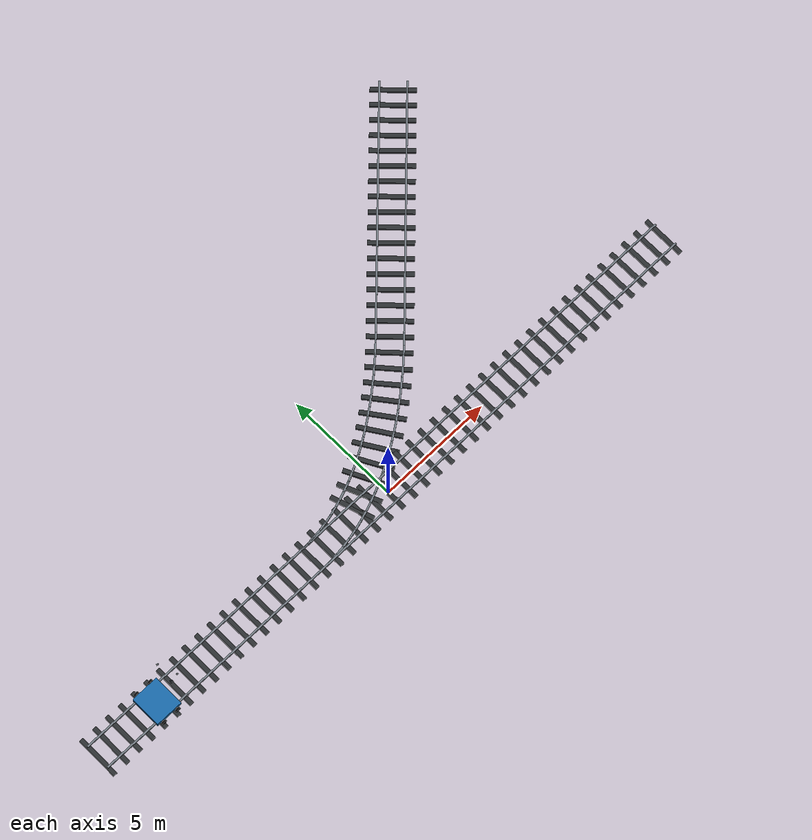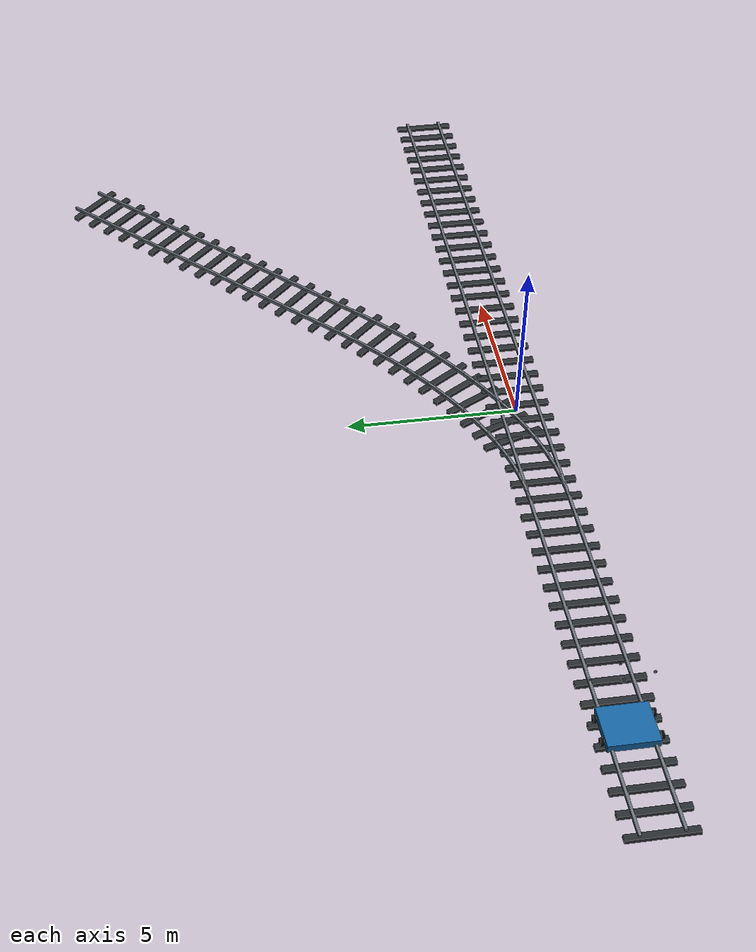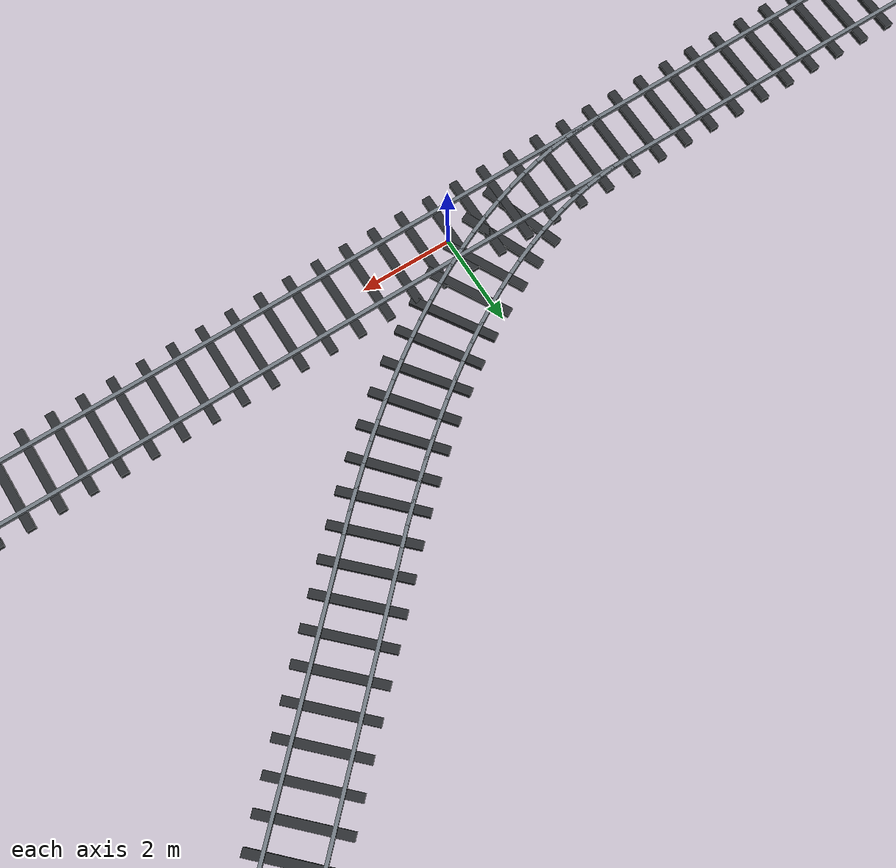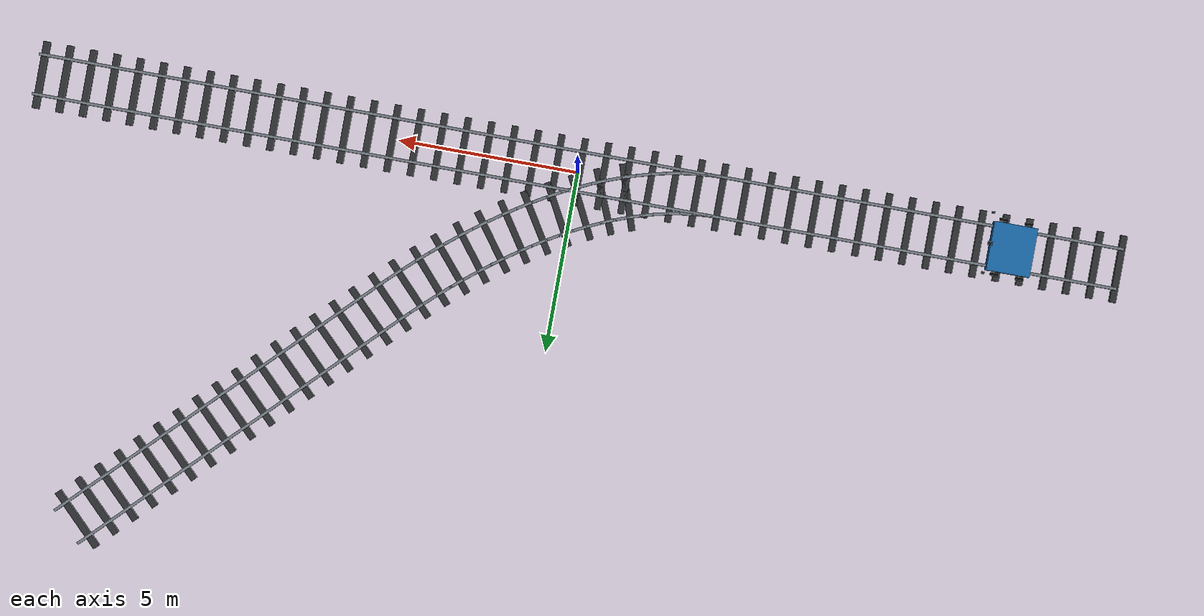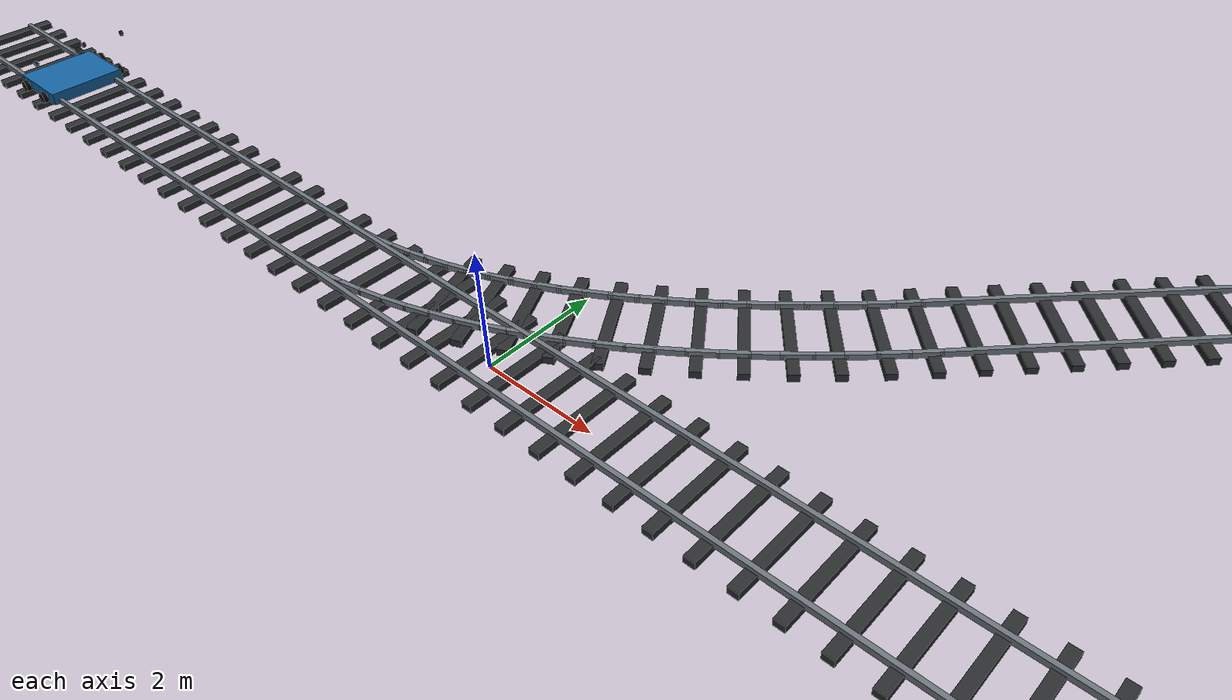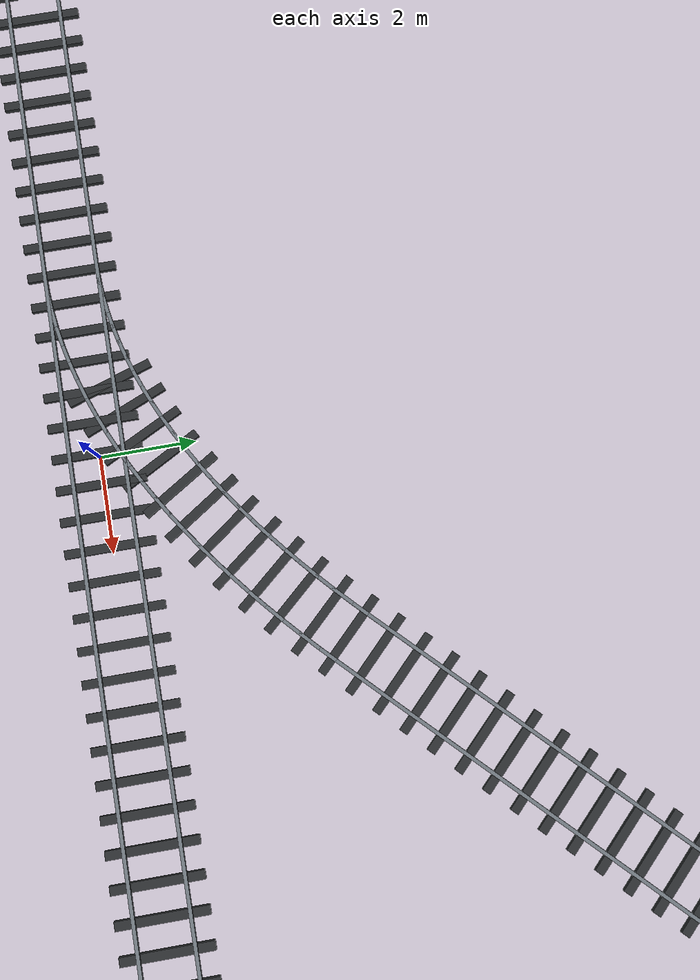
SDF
<?xml version='1.0' encoding='utf-8'?>
<sdf version="1.7">
  <world name="route_choice_training">
    <physics type="ode">
      <max_step_size>0.001</max_step_size>
      <real_time_factor>1</real_time_factor>
      <real_time_update_rate>1000</real_time_update_rate>
    </physics>
    <scene>
      <ambient>0.55 0.56 0.58 1</ambient>
      <background>0.07 0.08 0.09 1</background>
      <shadows>true</shadows>
      <grid>false</grid>
      <origin_visual>false</origin_visual>
    </scene>
    <gui fullscreen="0">
      <camera name="user_camera">
        <pose>-15 -15 15 0 0.58 0.78</pose>
        <view_controller>orbit</view_controller>
        <projection_type>perspective</projection_type>
      </camera>
    </gui>
    <light name="sun" type="directional">
      <cast_shadows>true</cast_shadows>
      <pose>0 0 20 0 0 0</pose>
      <diffuse>0.82 0.82 0.80 1</diffuse>
      <specular>0.20 0.20 0.20 1</specular>
      <direction>-0.35 0.20 -0.92</direction>
    </light>
    <model name="route_choice_track">
      <static>true</static>
      <link name="track_link">
        <visual name="main_rail_left_000">
          <pose>0.00000 0.55000 0.35000 0 0 0.0000000</pose>
          <geometry>
            <box>
              <size>30.06000 0.07500 0.10000</size>
            </box>
          </geometry>
          <material>
            <ambient>0.42 0.45 0.48 1</ambient>
            <diffuse>0.42 0.45 0.48 1</diffuse>
            <specular>0.35 0.35 0.35 1</specular>
          </material>
        </visual>
        <visual name="main_rail_right_000">
          <pose>0.00000 -0.55000 0.35000 0 0 0.0000000</pose>
          <geometry>
            <box>
              <size>30.06000 0.07500 0.10000</size>
            </box>
          </geometry>
          <material>
            <ambient>0.42 0.45 0.48 1</ambient>
            <diffuse>0.42 0.45 0.48 1</diffuse>
            <specular>0.35 0.35 0.35 1</specular>
          </material>
        </visual>
        <collision name="main_support_000">
          <pose>0.00000 0.00000 0.30500 0 0 0.0000000</pose>
          <geometry>
            <box>
              <size>30.06000 2.10 0.05000</size>
            </box>
          </geometry>
          <surface>
            <friction>
              <ode>
                <mu>1.0</mu>
                <mu2>1.0</mu2>
              </ode>
            </friction>
          </surface>
        </collision>
        <visual name="main_sleeper_000">
          <pose>-15.00000 0.00000 0.27000 0 0 0.0000000</pose>
          <geometry>
            <box>
              <size>0.18000 1.85000 0.12000</size>
            </box>
          </geometry>
          <material>
            <ambient>0.16 0.17 0.18 1</ambient>
            <diffuse>0.16 0.17 0.18 1</diffuse>
            <specular>0.35 0.35 0.35 1</specular>
          </material>
        </visual>
        <visual name="main_sleeper_001">
          <pose>-14.35000 0.00000 0.27000 0 0 0.0000000</pose>
          <geometry>
            <box>
              <size>0.18000 1.85000 0.12000</size>
            </box>
          </geometry>
          <material>
            <ambient>0.16 0.17 0.18 1</ambient>
            <diffuse>0.16 0.17 0.18 1</diffuse>
            <specular>0.35 0.35 0.35 1</specular>
          </material>
        </visual>
        <visual name="main_sleeper_002">
          <pose>-13.70000 0.00000 0.27000 0 0 0.0000000</pose>
          <geometry>
            <box>
              <size>0.18000 1.85000 0.12000</size>
            </box>
          </geometry>
          <material>
            <ambient>0.16 0.17 0.18 1</ambient>
            <diffuse>0.16 0.17 0.18 1</diffuse>
            <specular>0.35 0.35 0.35 1</specular>
          </material>
        </visual>
        <visual name="main_sleeper_003">
          <pose>-13.05000 0.00000 0.27000 0 0 0.0000000</pose>
          <geometry>
            <box>
              <size>0.18000 1.85000 0.12000</size>
            </box>
          </geometry>
          <material>
            <ambient>0.16 0.17 0.18 1</ambient>
            <diffuse>0.16 0.17 0.18 1</diffuse>
            <specular>0.35 0.35 0.35 1</specular>
          </material>
        </visual>
        <visual name="main_sleeper_004">
          <pose>-12.40000 0.00000 0.27000 0 0 0.0000000</pose>
          <geometry>
            <box>
              <size>0.18000 1.85000 0.12000</size>
            </box>
          </geometry>
          <material>
            <ambient>0.16 0.17 0.18 1</ambient>
            <diffuse>0.16 0.17 0.18 1</diffuse>
            <specular>0.35 0.35 0.35 1</specular>
          </material>
        </visual>
        <visual name="main_sleeper_005">
          <pose>-11.75000 0.00000 0.27000 0 0 0.0000000</pose>
          <geometry>
            <box>
              <size>0.18000 1.85000 0.12000</size>
            </box>
          </geometry>
          <material>
            <ambient>0.16 0.17 0.18 1</ambient>
            <diffuse>0.16 0.17 0.18 1</diffuse>
            <specular>0.35 0.35 0.35 1</specular>
          </material>
        </visual>
        <visual name="main_sleeper_006">
          <pose>-11.10000 0.00000 0.27000 0 0 0.0000000</pose>
          <geometry>
            <box>
              <size>0.18000 1.85000 0.12000</size>
            </box>
          </geometry>
          <material>
            <ambient>0.16 0.17 0.18 1</ambient>
            <diffuse>0.16 0.17 0.18 1</diffuse>
            <specular>0.35 0.35 0.35 1</specular>
          </material>
        </visual>
        <visual name="main_sleeper_007">
          <pose>-10.45000 0.00000 0.27000 0 0 0.0000000</pose>
          <geometry>
            <box>
              <size>0.18000 1.85000 0.12000</size>
            </box>
          </geometry>
          <material>
            <ambient>0.16 0.17 0.18 1</ambient>
            <diffuse>0.16 0.17 0.18 1</diffuse>
            <specular>0.35 0.35 0.35 1</specular>
          </material>
        </visual>
        <visual name="main_sleeper_008">
          <pose>-9.80000 0.00000 0.27000 0 0 0.0000000</pose>
          <geometry>
            <box>
              <size>0.18000 1.85000 0.12000</size>
            </box>
          </geometry>
          <material>
            <ambient>0.16 0.17 0.18 1</ambient>
            <diffuse>0.16 0.17 0.18 1</diffuse>
            <specular>0.35 0.35 0.35 1</specular>
          </material>
        </visual>
        <visual name="main_sleeper_009">
          <pose>-9.15000 0.00000 0.27000 0 0 0.0000000</pose>
          <geometry>
            <box>
              <size>0.18000 1.85000 0.12000</size>
            </box>
          </geometry>
          <material>
            <ambient>0.16 0.17 0.18 1</ambient>
            <diffuse>0.16 0.17 0.18 1</diffuse>
            <specular>0.35 0.35 0.35 1</specular>
          </material>
        </visual>
        <visual name="main_sleeper_010">
          <pose>-8.50000 0.00000 0.27000 0 0 0.0000000</pose>
          <geometry>
            <box>
              <size>0.18000 1.85000 0.12000</size>
            </box>
          </geometry>
          <material>
            <ambient>0.16 0.17 0.18 1</ambient>
            <diffuse>0.16 0.17 0.18 1</diffuse>
            <specular>0.35 0.35 0.35 1</specular>
          </material>
        </visual>
        <visual name="main_sleeper_011">
          <pose>-7.85000 0.00000 0.27000 0 0 0.0000000</pose>
          <geometry>
            <box>
              <size>0.18000 1.85000 0.12000</size>
            </box>
          </geometry>
          <material>
            <ambient>0.16 0.17 0.18 1</ambient>
            <diffuse>0.16 0.17 0.18 1</diffuse>
            <specular>0.35 0.35 0.35 1</specular>
          </material>
        </visual>
        <visual name="main_sleeper_012">
          <pose>-7.20000 0.00000 0.27000 0 0 0.0000000</pose>
          <geometry>
            <box>
              <size>0.18000 1.85000 0.12000</size>
            </box>
          </geometry>
          <material>
            <ambient>0.16 0.17 0.18 1</ambient>
            <diffuse>0.16 0.17 0.18 1</diffuse>
            <specular>0.35 0.35 0.35 1</specular>
          </material>
        </visual>
        <visual name="main_sleeper_013">
          <pose>-6.55000 0.00000 0.27000 0 0 0.0000000</pose>
          <geometry>
            <box>
              <size>0.18000 1.85000 0.12000</size>
            </box>
          </geometry>
          <material>
            <ambient>0.16 0.17 0.18 1</ambient>
            <diffuse>0.16 0.17 0.18 1</diffuse>
            <specular>0.35 0.35 0.35 1</specular>
          </material>
        </visual>
        <visual name="main_sleeper_014">
          <pose>-5.90000 0.00000 0.27000 0 0 0.0000000</pose>
          <geometry>
            <box>
              <size>0.18000 1.85000 0.12000</size>
            </box>
          </geometry>
          <material>
            <ambient>0.16 0.17 0.18 1</ambient>
            <diffuse>0.16 0.17 0.18 1</diffuse>
            <specular>0.35 0.35 0.35 1</specular>
          </material>
        </visual>
        <visual name="main_sleeper_015">
          <pose>-5.25000 0.00000 0.27000 0 0 0.0000000</pose>
          <geometry>
            <box>
              <size>0.18000 1.85000 0.12000</size>
            </box>
          </geometry>
          <material>
            <ambient>0.16 0.17 0.18 1</ambient>
            <diffuse>0.16 0.17 0.18 1</diffuse>
            <specular>0.35 0.35 0.35 1</specular>
          </material>
        </visual>
        <visual name="main_sleeper_016">
          <pose>-4.60000 0.00000 0.27000 0 0 0.0000000</pose>
          <geometry>
            <box>
              <size>0.18000 1.85000 0.12000</size>
            </box>
          </geometry>
          <material>
            <ambient>0.16 0.17 0.18 1</ambient>
            <diffuse>0.16 0.17 0.18 1</diffuse>
            <specular>0.35 0.35 0.35 1</specular>
          </material>
        </visual>
        <visual name="main_sleeper_017">
          <pose>-3.95000 0.00000 0.27000 0 0 0.0000000</pose>
          <geometry>
            <box>
              <size>0.18000 1.85000 0.12000</size>
            </box>
          </geometry>
          <material>
            <ambient>0.16 0.17 0.18 1</ambient>
            <diffuse>0.16 0.17 0.18 1</diffuse>
            <specular>0.35 0.35 0.35 1</specular>
          </material>
        </visual>
        <visual name="main_sleeper_018">
          <pose>-3.30000 0.00000 0.27000 0 0 0.0000000</pose>
          <geometry>
            <box>
              <size>0.18000 1.85000 0.12000</size>
            </box>
          </geometry>
          <material>
            <ambient>0.16 0.17 0.18 1</ambient>
            <diffuse>0.16 0.17 0.18 1</diffuse>
            <specular>0.35 0.35 0.35 1</specular>
          </material>
        </visual>
        <visual name="main_sleeper_019">
          <pose>-2.65000 0.00000 0.27000 0 0 0.0000000</pose>
          <geometry>
            <box>
              <size>0.18000 1.85000 0.12000</size>
            </box>
          </geometry>
          <material>
            <ambient>0.16 0.17 0.18 1</ambient>
            <diffuse>0.16 0.17 0.18 1</diffuse>
            <specular>0.35 0.35 0.35 1</specular>
          </material>
        </visual>
        <visual name="main_sleeper_020">
          <pose>-2.00000 0.00000 0.27000 0 0 0.0000000</pose>
          <geometry>
            <box>
              <size>0.18000 1.85000 0.12000</size>
            </box>
          </geometry>
          <material>
            <ambient>0.16 0.17 0.18 1</ambient>
            <diffuse>0.16 0.17 0.18 1</diffuse>
            <specular>0.35 0.35 0.35 1</specular>
          </material>
        </visual>
        <visual name="main_sleeper_021">
          <pose>-1.35000 0.00000 0.27000 0 0 0.0000000</pose>
          <geometry>
            <box>
              <size>0.18000 1.85000 0.12000</size>
            </box>
          </geometry>
          <material>
            <ambient>0.16 0.17 0.18 1</ambient>
            <diffuse>0.16 0.17 0.18 1</diffuse>
            <specular>0.35 0.35 0.35 1</specular>
          </material>
        </visual>
        <visual name="main_sleeper_022">
          <pose>-0.70000 0.00000 0.27000 0 0 0.0000000</pose>
          <geometry>
            <box>
              <size>0.18000 1.85000 0.12000</size>
            </box>
          </geometry>
          <material>
            <ambient>0.16 0.17 0.18 1</ambient>
            <diffuse>0.16 0.17 0.18 1</diffuse>
            <specular>0.35 0.35 0.35 1</specular>
          </material>
        </visual>
        <visual name="main_sleeper_023">
          <pose>-0.05000 0.00000 0.27000 0 0 0.0000000</pose>
          <geometry>
            <box>
              <size>0.18000 1.85000 0.12000</size>
            </box>
          </geometry>
          <material>
            <ambient>0.16 0.17 0.18 1</ambient>
            <diffuse>0.16 0.17 0.18 1</diffuse>
            <specular>0.35 0.35 0.35 1</specular>
          </material>
        </visual>
        <visual name="main_sleeper_024">
          <pose>0.60000 0.00000 0.27000 0 0 0.0000000</pose>
          <geometry>
            <box>
              <size>0.18000 1.85000 0.12000</size>
            </box>
          </geometry>
          <material>
            <ambient>0.16 0.17 0.18 1</ambient>
            <diffuse>0.16 0.17 0.18 1</diffuse>
            <specular>0.35 0.35 0.35 1</specular>
          </material>
        </visual>
        <visual name="main_sleeper_025">
          <pose>1.25000 0.00000 0.27000 0 0 0.0000000</pose>
          <geometry>
            <box>
              <size>0.18000 1.85000 0.12000</size>
            </box>
          </geometry>
          <material>
            <ambient>0.16 0.17 0.18 1</ambient>
            <diffuse>0.16 0.17 0.18 1</diffuse>
            <specular>0.35 0.35 0.35 1</specular>
          </material>
        </visual>
        <visual name="main_sleeper_026">
          <pose>1.90000 0.00000 0.27000 0 0 0.0000000</pose>
          <geometry>
            <box>
              <size>0.18000 1.85000 0.12000</size>
            </box>
          </geometry>
          <material>
            <ambient>0.16 0.17 0.18 1</ambient>
            <diffuse>0.16 0.17 0.18 1</diffuse>
            <specular>0.35 0.35 0.35 1</specular>
          </material>
        </visual>
        <visual name="main_sleeper_027">
          <pose>2.55000 0.00000 0.27000 0 0 0.0000000</pose>
          <geometry>
            <box>
              <size>0.18000 1.85000 0.12000</size>
            </box>
          </geometry>
          <material>
            <ambient>0.16 0.17 0.18 1</ambient>
            <diffuse>0.16 0.17 0.18 1</diffuse>
            <specular>0.35 0.35 0.35 1</specular>
          </material>
        </visual>
        <visual name="main_sleeper_028">
          <pose>3.20000 0.00000 0.27000 0 0 0.0000000</pose>
          <geometry>
            <box>
              <size>0.18000 1.85000 0.12000</size>
            </box>
          </geometry>
          <material>
            <ambient>0.16 0.17 0.18 1</ambient>
            <diffuse>0.16 0.17 0.18 1</diffuse>
            <specular>0.35 0.35 0.35 1</specular>
          </material>
        </visual>
        <visual name="main_sleeper_029">
          <pose>3.85000 0.00000 0.27000 0 0 0.0000000</pose>
          <geometry>
            <box>
              <size>0.18000 1.85000 0.12000</size>
            </box>
          </geometry>
          <material>
            <ambient>0.16 0.17 0.18 1</ambient>
            <diffuse>0.16 0.17 0.18 1</diffuse>
            <specular>0.35 0.35 0.35 1</specular>
          </material>
        </visual>
        <visual name="main_sleeper_030">
          <pose>4.50000 0.00000 0.27000 0 0 0.0000000</pose>
          <geometry>
            <box>
              <size>0.18000 1.85000 0.12000</size>
            </box>
          </geometry>
          <material>
            <ambient>0.16 0.17 0.18 1</ambient>
            <diffuse>0.16 0.17 0.18 1</diffuse>
            <specular>0.35 0.35 0.35 1</specular>
          </material>
        </visual>
        <visual name="main_sleeper_031">
          <pose>5.15000 0.00000 0.27000 0 0 0.0000000</pose>
          <geometry>
            <box>
              <size>0.18000 1.85000 0.12000</size>
            </box>
          </geometry>
          <material>
            <ambient>0.16 0.17 0.18 1</ambient>
            <diffuse>0.16 0.17 0.18 1</diffuse>
            <specular>0.35 0.35 0.35 1</specular>
          </material>
        </visual>
        <visual name="main_sleeper_032">
          <pose>5.80000 0.00000 0.27000 0 0 0.0000000</pose>
          <geometry>
            <box>
              <size>0.18000 1.85000 0.12000</size>
            </box>
          </geometry>
          <material>
            <ambient>0.16 0.17 0.18 1</ambient>
            <diffuse>0.16 0.17 0.18 1</diffuse>
            <specular>0.35 0.35 0.35 1</specular>
          </material>
        </visual>
        <visual name="main_sleeper_033">
          <pose>6.45000 0.00000 0.27000 0 0 0.0000000</pose>
          <geometry>
            <box>
              <size>0.18000 1.85000 0.12000</size>
            </box>
          </geometry>
          <material>
            <ambient>0.16 0.17 0.18 1</ambient>
            <diffuse>0.16 0.17 0.18 1</diffuse>
            <specular>0.35 0.35 0.35 1</specular>
          </material>
        </visual>
        <visual name="main_sleeper_034">
          <pose>7.10000 0.00000 0.27000 0 0 0.0000000</pose>
          <geometry>
            <box>
              <size>0.18000 1.85000 0.12000</size>
            </box>
          </geometry>
          <material>
            <ambient>0.16 0.17 0.18 1</ambient>
            <diffuse>0.16 0.17 0.18 1</diffuse>
            <specular>0.35 0.35 0.35 1</specular>
          </material>
        </visual>
        <visual name="main_sleeper_035">
          <pose>7.75000 0.00000 0.27000 0 0 0.0000000</pose>
          <geometry>
            <box>
              <size>0.18000 1.85000 0.12000</size>
            </box>
          </geometry>
          <material>
            <ambient>0.16 0.17 0.18 1</ambient>
            <diffuse>0.16 0.17 0.18 1</diffuse>
            <specular>0.35 0.35 0.35 1</specular>
          </material>
        </visual>
        <visual name="main_sleeper_036">
          <pose>8.40000 0.00000 0.27000 0 0 0.0000000</pose>
          <geometry>
            <box>
              <size>0.18000 1.85000 0.12000</size>
            </box>
          </geometry>
          <material>
            <ambient>0.16 0.17 0.18 1</ambient>
            <diffuse>0.16 0.17 0.18 1</diffuse>
            <specular>0.35 0.35 0.35 1</specular>
          </material>
        </visual>
        <visual name="main_sleeper_037">
          <pose>9.05000 0.00000 0.27000 0 0 0.0000000</pose>
          <geometry>
            <box>
              <size>0.18000 1.85000 0.12000</size>
            </box>
          </geometry>
          <material>
            <ambient>0.16 0.17 0.18 1</ambient>
            <diffuse>0.16 0.17 0.18 1</diffuse>
            <specular>0.35 0.35 0.35 1</specular>
          </material>
        </visual>
        <visual name="main_sleeper_038">
          <pose>9.70000 0.00000 0.27000 0 0 0.0000000</pose>
          <geometry>
            <box>
              <size>0.18000 1.85000 0.12000</size>
            </box>
          </geometry>
          <material>
            <ambient>0.16 0.17 0.18 1</ambient>
            <diffuse>0.16 0.17 0.18 1</diffuse>
            <specular>0.35 0.35 0.35 1</specular>
          </material>
        </visual>
        <visual name="main_sleeper_039">
          <pose>10.35000 0.00000 0.27000 0 0 0.0000000</pose>
          <geometry>
            <box>
              <size>0.18000 1.85000 0.12000</size>
            </box>
          </geometry>
          <material>
            <ambient>0.16 0.17 0.18 1</ambient>
            <diffuse>0.16 0.17 0.18 1</diffuse>
            <specular>0.35 0.35 0.35 1</specular>
          </material>
        </visual>
        <visual name="main_sleeper_040">
          <pose>11.00000 0.00000 0.27000 0 0 0.0000000</pose>
          <geometry>
            <box>
              <size>0.18000 1.85000 0.12000</size>
            </box>
          </geometry>
          <material>
            <ambient>0.16 0.17 0.18 1</ambient>
            <diffuse>0.16 0.17 0.18 1</diffuse>
            <specular>0.35 0.35 0.35 1</specular>
          </material>
        </visual>
        <visual name="main_sleeper_041">
          <pose>11.65000 0.00000 0.27000 0 0 0.0000000</pose>
          <geometry>
            <box>
              <size>0.18000 1.85000 0.12000</size>
            </box>
          </geometry>
          <material>
            <ambient>0.16 0.17 0.18 1</ambient>
            <diffuse>0.16 0.17 0.18 1</diffuse>
            <specular>0.35 0.35 0.35 1</specular>
          </material>
        </visual>
        <visual name="main_sleeper_042">
          <pose>12.30000 0.00000 0.27000 0 0 0.0000000</pose>
          <geometry>
            <box>
              <size>0.18000 1.85000 0.12000</size>
            </box>
          </geometry>
          <material>
            <ambient>0.16 0.17 0.18 1</ambient>
            <diffuse>0.16 0.17 0.18 1</diffuse>
            <specular>0.35 0.35 0.35 1</specular>
          </material>
        </visual>
        <visual name="main_sleeper_043">
          <pose>12.95000 0.00000 0.27000 0 0 0.0000000</pose>
          <geometry>
            <box>
              <size>0.18000 1.85000 0.12000</size>
            </box>
          </geometry>
          <material>
            <ambient>0.16 0.17 0.18 1</ambient>
            <diffuse>0.16 0.17 0.18 1</diffuse>
            <specular>0.35 0.35 0.35 1</specular>
          </material>
        </visual>
        <visual name="main_sleeper_044">
          <pose>13.60000 0.00000 0.27000 0 0 0.0000000</pose>
          <geometry>
            <box>
              <size>0.18000 1.85000 0.12000</size>
            </box>
          </geometry>
          <material>
            <ambient>0.16 0.17 0.18 1</ambient>
            <diffuse>0.16 0.17 0.18 1</diffuse>
            <specular>0.35 0.35 0.35 1</specular>
          </material>
        </visual>
        <visual name="main_sleeper_045">
          <pose>14.25000 0.00000 0.27000 0 0 0.0000000</pose>
          <geometry>
            <box>
              <size>0.18000 1.85000 0.12000</size>
            </box>
          </geometry>
          <material>
            <ambient>0.16 0.17 0.18 1</ambient>
            <diffuse>0.16 0.17 0.18 1</diffuse>
            <specular>0.35 0.35 0.35 1</specular>
          </material>
        </visual>
        <visual name="main_sleeper_046">
          <pose>14.90000 0.00000 0.27000 0 0 0.0000000</pose>
          <geometry>
            <box>
              <size>0.18000 1.85000 0.12000</size>
            </box>
          </geometry>
          <material>
            <ambient>0.16 0.17 0.18 1</ambient>
            <diffuse>0.16 0.17 0.18 1</diffuse>
            <specular>0.35 0.35 0.35 1</specular>
          </material>
        </visual>
        <visual name="branch_rail_left_000">
          <pose>-3.82763 0.55495 0.35000 0 0 0.0274842</pose>
          <geometry>
            <box>
              <size>0.43511 0.07500 0.10000</size>
            </box>
          </geometry>
          <material>
            <ambient>0.42 0.45 0.48 1</ambient>
            <diffuse>0.42 0.45 0.48 1</diffuse>
            <specular>0.35 0.35 0.35 1</specular>
          </material>
        </visual>
        <visual name="branch_rail_right_000">
          <pose>-3.79740 -0.54464 0.35000 0 0 0.0274842</pose>
          <geometry>
            <box>
              <size>0.43511 0.07500 0.10000</size>
            </box>
          </geometry>
          <material>
            <ambient>0.42 0.45 0.48 1</ambient>
            <diffuse>0.42 0.45 0.48 1</diffuse>
            <specular>0.35 0.35 0.35 1</specular>
          </material>
        </visual>
        <collision name="branch_support_000">
          <pose>-3.81252 0.00515 0.30500 0 0 0.0274842</pose>
          <geometry>
            <box>
              <size>0.43511 2.10 0.05000</size>
            </box>
          </geometry>
          <surface>
            <friction>
              <ode>
                <mu>1.0</mu>
                <mu2>1.0</mu2>
              </ode>
            </friction>
          </surface>
        </collision>
        <visual name="branch_rail_left_001">
          <pose>-3.48226 0.57374 0.35000 0 0 0.0811840</pose>
          <geometry>
            <box>
              <size>0.43599 0.07500 0.10000</size>
            </box>
          </geometry>
          <material>
            <ambient>0.42 0.45 0.48 1</ambient>
            <diffuse>0.42 0.45 0.48 1</diffuse>
            <specular>0.35 0.35 0.35 1</specular>
          </material>
        </visual>
        <visual name="branch_rail_right_001">
          <pose>-3.39306 -0.52264 0.35000 0 0 0.0811840</pose>
          <geometry>
            <box>
              <size>0.43599 0.07500 0.10000</size>
            </box>
          </geometry>
          <material>
            <ambient>0.42 0.45 0.48 1</ambient>
            <diffuse>0.42 0.45 0.48 1</diffuse>
            <specular>0.35 0.35 0.35 1</specular>
          </material>
        </visual>
        <collision name="branch_support_001">
          <pose>-3.43766 0.02555 0.30500 0 0 0.0811840</pose>
          <geometry>
            <box>
              <size>0.43599 2.10 0.05000</size>
            </box>
          </geometry>
          <surface>
            <friction>
              <ode>
                <mu>1.0</mu>
                <mu2>1.0</mu2>
              </ode>
            </friction>
          </surface>
        </collision>
        <visual name="branch_rail_left_002">
          <pose>-3.13599 0.61096 0.35000 0 0 0.1328490</pose>
          <geometry>
            <box>
              <size>0.43764 0.07500 0.10000</size>
            </box>
          </geometry>
          <material>
            <ambient>0.42 0.45 0.48 1</ambient>
            <diffuse>0.42 0.45 0.48 1</diffuse>
            <specular>0.35 0.35 0.35 1</specular>
          </material>
        </visual>
        <visual name="branch_rail_right_002">
          <pose>-2.99028 -0.47934 0.35000 0 0 0.1328490</pose>
          <geometry>
            <box>
              <size>0.43764 0.07500 0.10000</size>
            </box>
          </geometry>
          <material>
            <ambient>0.42 0.45 0.48 1</ambient>
            <diffuse>0.42 0.45 0.48 1</diffuse>
            <specular>0.35 0.35 0.35 1</specular>
          </material>
        </visual>
        <collision name="branch_support_002">
          <pose>-3.06313 0.06581 0.30500 0 0 0.1328490</pose>
          <geometry>
            <box>
              <size>0.43764 2.10 0.05000</size>
            </box>
          </geometry>
          <surface>
            <friction>
              <ode>
                <mu>1.0</mu>
                <mu2>1.0</mu2>
              </ode>
            </friction>
          </surface>
        </collision>
        <visual name="branch_rail_left_003">
          <pose>-2.78888 0.66615 0.35000 0 0 0.1823482</pose>
          <geometry>
            <box>
              <size>0.43996 0.07500 0.10000</size>
            </box>
          </geometry>
          <material>
            <ambient>0.42 0.45 0.48 1</ambient>
            <diffuse>0.42 0.45 0.48 1</diffuse>
            <specular>0.35 0.35 0.35 1</specular>
          </material>
        </visual>
        <visual name="branch_rail_right_003">
          <pose>-2.58941 -0.41561 0.35000 0 0 0.1823482</pose>
          <geometry>
            <box>
              <size>0.43996 0.07500 0.10000</size>
            </box>
          </geometry>
          <material>
            <ambient>0.42 0.45 0.48 1</ambient>
            <diffuse>0.42 0.45 0.48 1</diffuse>
            <specular>0.35 0.35 0.35 1</specular>
          </material>
        </visual>
        <collision name="branch_support_003">
          <pose>-2.68915 0.12527 0.30500 0 0 0.1823482</pose>
          <geometry>
            <box>
              <size>0.43996 2.10 0.05000</size>
            </box>
          </geometry>
          <surface>
            <friction>
              <ode>
                <mu>1.0</mu>
                <mu2>1.0</mu2>
              </ode>
            </friction>
          </surface>
        </collision>
        <visual name="branch_rail_left_004">
          <pose>-2.44109 0.73885 0.35000 0 0 0.2296030</pose>
          <geometry>
            <box>
              <size>0.44284 0.07500 0.10000</size>
            </box>
          </geometry>
          <material>
            <ambient>0.42 0.45 0.48 1</ambient>
            <diffuse>0.42 0.45 0.48 1</diffuse>
            <specular>0.35 0.35 0.35 1</specular>
          </material>
        </visual>
        <visual name="branch_rail_right_004">
          <pose>-2.19074 -0.33228 0.35000 0 0 0.2296030</pose>
          <geometry>
            <box>
              <size>0.44284 0.07500 0.10000</size>
            </box>
          </geometry>
          <material>
            <ambient>0.42 0.45 0.48 1</ambient>
            <diffuse>0.42 0.45 0.48 1</diffuse>
            <specular>0.35 0.35 0.35 1</specular>
          </material>
        </visual>
        <collision name="branch_support_004">
          <pose>-2.31592 0.20329 0.30500 0 0 0.2296030</pose>
          <geometry>
            <box>
              <size>0.44284 2.10 0.05000</size>
            </box>
          </geometry>
          <surface>
            <friction>
              <ode>
                <mu>1.0</mu>
                <mu2>1.0</mu2>
              </ode>
            </friction>
          </surface>
        </collision>
        <visual name="branch_rail_left_005">
          <pose>-2.09280 0.82860 0.35000 0 0 0.2745816</pose>
          <geometry>
            <box>
              <size>0.44618 0.07500 0.10000</size>
            </box>
          </geometry>
          <material>
            <ambient>0.42 0.45 0.48 1</ambient>
            <diffuse>0.42 0.45 0.48 1</diffuse>
            <specular>0.35 0.35 0.35 1</specular>
          </material>
        </visual>
        <visual name="branch_rail_right_005">
          <pose>-1.79454 -0.23019 0.35000 0 0 0.2745816</pose>
          <geometry>
            <box>
              <size>0.44618 0.07500 0.10000</size>
            </box>
          </geometry>
          <material>
            <ambient>0.42 0.45 0.48 1</ambient>
            <diffuse>0.42 0.45 0.48 1</diffuse>
            <specular>0.35 0.35 0.35 1</specular>
          </material>
        </visual>
        <collision name="branch_support_005">
          <pose>-1.94367 0.29921 0.30500 0 0 0.2745816</pose>
          <geometry>
            <box>
              <size>0.44618 2.10 0.05000</size>
            </box>
          </geometry>
          <surface>
            <friction>
              <ode>
                <mu>1.0</mu>
                <mu2>1.0</mu2>
              </ode>
            </friction>
          </surface>
        </collision>
        <visual name="branch_rail_left_006">
          <pose>-1.74421 0.93493 0.35000 0 0 0.3172913</pose>
          <geometry>
            <box>
              <size>0.44987 0.07500 0.10000</size>
            </box>
          </geometry>
          <material>
            <ambient>0.42 0.45 0.48 1</ambient>
            <diffuse>0.42 0.45 0.48 1</diffuse>
            <specular>0.35 0.35 0.35 1</specular>
          </material>
        </visual>
        <visual name="branch_rail_right_006">
          <pose>-1.40101 -0.11017 0.35000 0 0 0.3172913</pose>
          <geometry>
            <box>
              <size>0.44987 0.07500 0.10000</size>
            </box>
          </geometry>
          <material>
            <ambient>0.42 0.45 0.48 1</ambient>
            <diffuse>0.42 0.45 0.48 1</diffuse>
            <specular>0.35 0.35 0.35 1</specular>
          </material>
        </visual>
        <collision name="branch_support_006">
          <pose>-1.57261 0.41238 0.30500 0 0 0.3172913</pose>
          <geometry>
            <box>
              <size>0.44987 2.10 0.05000</size>
            </box>
          </geometry>
          <surface>
            <friction>
              <ode>
                <mu>1.0</mu>
                <mu2>1.0</mu2>
              </ode>
            </friction>
          </surface>
        </collision>
        <visual name="branch_rail_left_007">
          <pose>-1.39557 1.05733 0.35000 0 0 0.3577710</pose>
          <geometry>
            <box>
              <size>0.45382 0.07500 0.10000</size>
            </box>
          </geometry>
          <material>
            <ambient>0.42 0.45 0.48 1</ambient>
            <diffuse>0.42 0.45 0.48 1</diffuse>
            <specular>0.35 0.35 0.35 1</specular>
          </material>
        </visual>
        <visual name="branch_rail_right_007">
          <pose>-1.01036 0.02698 0.35000 0 0 0.3577710</pose>
          <geometry>
            <box>
              <size>0.45382 0.07500 0.10000</size>
            </box>
          </geometry>
          <material>
            <ambient>0.42 0.45 0.48 1</ambient>
            <diffuse>0.42 0.45 0.48 1</diffuse>
            <specular>0.35 0.35 0.35 1</specular>
          </material>
        </visual>
        <collision name="branch_support_007">
          <pose>-1.20296 0.54215 0.30500 0 0 0.3577710</pose>
          <geometry>
            <box>
              <size>0.45382 2.10 0.05000</size>
            </box>
          </geometry>
          <surface>
            <friction>
              <ode>
                <mu>1.0</mu>
                <mu2>1.0</mu2>
              </ode>
            </friction>
          </surface>
        </collision>
        <visual name="branch_rail_left_008">
          <pose>-1.04714 1.19530 0.35000 0 0 0.3960845</pose>
          <geometry>
            <box>
              <size>0.45796 0.07500 0.10000</size>
            </box>
          </geometry>
          <material>
            <ambient>0.42 0.45 0.48 1</ambient>
            <diffuse>0.42 0.45 0.48 1</diffuse>
            <specular>0.35 0.35 0.35 1</specular>
          </material>
        </visual>
        <visual name="branch_rail_right_008">
          <pose>-0.62275 0.18046 0.35000 0 0 0.3960845</pose>
          <geometry>
            <box>
              <size>0.45796 0.07500 0.10000</size>
            </box>
          </geometry>
          <material>
            <ambient>0.42 0.45 0.48 1</ambient>
            <diffuse>0.42 0.45 0.48 1</diffuse>
            <specular>0.35 0.35 0.35 1</specular>
          </material>
        </visual>
        <collision name="branch_support_008">
          <pose>-0.83494 0.68788 0.30500 0 0 0.3960845</pose>
          <geometry>
            <box>
              <size>0.45796 2.10 0.05000</size>
            </box>
          </geometry>
          <surface>
            <friction>
              <ode>
                <mu>1.0</mu>
                <mu2>1.0</mu2>
              </ode>
            </friction>
          </surface>
        </collision>
        <visual name="branch_rail_left_009">
          <pose>-0.69920 1.34830 0.35000 0 0 0.4323136</pose>
          <geometry>
            <box>
              <size>0.46220 0.07500 0.10000</size>
            </box>
          </geometry>
          <material>
            <ambient>0.42 0.45 0.48 1</ambient>
            <diffuse>0.42 0.45 0.48 1</diffuse>
            <specular>0.35 0.35 0.35 1</specular>
          </material>
        </visual>
        <visual name="branch_rail_right_009">
          <pose>-0.23833 0.34950 0.35000 0 0 0.4323136</pose>
          <geometry>
            <box>
              <size>0.46220 0.07500 0.10000</size>
            </box>
          </geometry>
          <material>
            <ambient>0.42 0.45 0.48 1</ambient>
            <diffuse>0.42 0.45 0.48 1</diffuse>
            <specular>0.35 0.35 0.35 1</specular>
          </material>
        </visual>
        <collision name="branch_support_009">
          <pose>-0.46877 0.84890 0.30500 0 0 0.4323136</pose>
          <geometry>
            <box>
              <size>0.46220 2.10 0.05000</size>
            </box>
          </geometry>
          <surface>
            <friction>
              <ode>
                <mu>1.0</mu>
                <mu2>1.0</mu2>
              </ode>
            </friction>
          </surface>
        </collision>
        <visual name="branch_rail_left_010">
          <pose>-0.35205 1.51580 0.35000 0 0 0.4665526</pose>
          <geometry>
            <box>
              <size>0.46647 0.07500 0.10000</size>
            </box>
          </geometry>
          <material>
            <ambient>0.42 0.45 0.48 1</ambient>
            <diffuse>0.42 0.45 0.48 1</diffuse>
            <specular>0.35 0.35 0.35 1</specular>
          </material>
        </visual>
        <visual name="branch_rail_right_010">
          <pose>0.14274 0.53336 0.35000 0 0 0.4665526</pose>
          <geometry>
            <box>
              <size>0.46647 0.07500 0.10000</size>
            </box>
          </geometry>
          <material>
            <ambient>0.42 0.45 0.48 1</ambient>
            <diffuse>0.42 0.45 0.48 1</diffuse>
            <specular>0.35 0.35 0.35 1</specular>
          </material>
        </visual>
        <collision name="branch_support_010">
          <pose>-0.10465 1.02458 0.30500 0 0 0.4665526</pose>
          <geometry>
            <box>
              <size>0.46647 2.10 0.05000</size>
            </box>
          </geometry>
          <surface>
            <friction>
              <ode>
                <mu>1.0</mu>
                <mu2>1.0</mu2>
              </ode>
            </friction>
          </surface>
        </collision>
        <visual name="branch_rail_left_011">
          <pose>-0.00598 1.69721 0.35000 0 0 0.4989039</pose>
          <geometry>
            <box>
              <size>0.47070 0.07500 0.10000</size>
            </box>
          </geometry>
          <material>
            <ambient>0.42 0.45 0.48 1</ambient>
            <diffuse>0.42 0.45 0.48 1</diffuse>
            <specular>0.35 0.35 0.35 1</specular>
          </material>
        </visual>
        <visual name="branch_rail_right_011">
          <pose>0.52033 0.73129 0.35000 0 0 0.4989039</pose>
          <geometry>
            <box>
              <size>0.47070 0.07500 0.10000</size>
            </box>
          </geometry>
          <material>
            <ambient>0.42 0.45 0.48 1</ambient>
            <diffuse>0.42 0.45 0.48 1</diffuse>
            <specular>0.35 0.35 0.35 1</specular>
          </material>
        </visual>
        <collision name="branch_support_011">
          <pose>0.25718 1.21425 0.30500 0 0 0.4989039</pose>
          <geometry>
            <box>
              <size>0.47070 2.10 0.05000</size>
            </box>
          </geometry>
          <surface>
            <friction>
              <ode>
                <mu>1.0</mu>
                <mu2>1.0</mu2>
              </ode>
            </friction>
          </surface>
        </collision>
        <visual name="branch_rail_left_012">
          <pose>0.33872 1.89195 0.35000 0 0 0.5294740</pose>
          <geometry>
            <box>
              <size>0.47484 0.07500 0.10000</size>
            </box>
          </geometry>
          <material>
            <ambient>0.42 0.45 0.48 1</ambient>
            <diffuse>0.42 0.45 0.48 1</diffuse>
            <specular>0.35 0.35 0.35 1</specular>
          </material>
        </visual>
        <visual name="branch_rail_right_012">
          <pose>0.89431 0.94257 0.35000 0 0 0.5294740</pose>
          <geometry>
            <box>
              <size>0.47484 0.07500 0.10000</size>
            </box>
          </geometry>
          <material>
            <ambient>0.42 0.45 0.48 1</ambient>
            <diffuse>0.42 0.45 0.48 1</diffuse>
            <specular>0.35 0.35 0.35 1</specular>
          </material>
        </visual>
        <collision name="branch_support_012">
          <pose>0.61652 1.41726 0.30500 0 0 0.5294740</pose>
          <geometry>
            <box>
              <size>0.47484 2.10 0.05000</size>
            </box>
          </geometry>
          <surface>
            <friction>
              <ode>
                <mu>1.0</mu>
                <mu2>1.0</mu2>
              </ode>
            </friction>
          </surface>
        </collision>
        <visual name="branch_rail_left_013">
          <pose>0.68175 2.09944 0.35000 0 0 0.5583705</pose>
          <geometry>
            <box>
              <size>0.47883 0.07500 0.10000</size>
            </box>
          </geometry>
          <material>
            <ambient>0.42 0.45 0.48 1</ambient>
            <diffuse>0.42 0.45 0.48 1</diffuse>
            <specular>0.35 0.35 0.35 1</specular>
          </material>
        </visual>
        <visual name="branch_rail_right_013">
          <pose>1.26454 1.16651 0.35000 0 0 0.5583705</pose>
          <geometry>
            <box>
              <size>0.47883 0.07500 0.10000</size>
            </box>
          </geometry>
          <material>
            <ambient>0.42 0.45 0.48 1</ambient>
            <diffuse>0.42 0.45 0.48 1</diffuse>
            <specular>0.35 0.35 0.35 1</specular>
          </material>
        </visual>
        <collision name="branch_support_013">
          <pose>0.97314 1.63298 0.30500 0 0 0.5583705</pose>
          <geometry>
            <box>
              <size>0.47883 2.10 0.05000</size>
            </box>
          </geometry>
          <surface>
            <friction>
              <ode>
                <mu>1.0</mu>
                <mu2>1.0</mu2>
              </ode>
            </friction>
          </surface>
        </collision>
        <visual name="branch_rail_left_014">
          <pose>1.02281 2.31906 0.35000 0 0 0.5857002</pose>
          <geometry>
            <box>
              <size>0.48262 0.07500 0.10000</size>
            </box>
          </geometry>
          <material>
            <ambient>0.42 0.45 0.48 1</ambient>
            <diffuse>0.42 0.45 0.48 1</diffuse>
            <specular>0.35 0.35 0.35 1</specular>
          </material>
        </visual>
        <visual name="branch_rail_right_014">
          <pose>1.63087 1.40240 0.35000 0 0 0.5857002</pose>
          <geometry>
            <box>
              <size>0.48262 0.07500 0.10000</size>
            </box>
          </geometry>
          <material>
            <ambient>0.42 0.45 0.48 1</ambient>
            <diffuse>0.42 0.45 0.48 1</diffuse>
            <specular>0.35 0.35 0.35 1</specular>
          </material>
        </visual>
        <collision name="branch_support_014">
          <pose>1.32684 1.86073 0.30500 0 0 0.5857002</pose>
          <geometry>
            <box>
              <size>0.48262 2.10 0.05000</size>
            </box>
          </geometry>
          <surface>
            <friction>
              <ode>
                <mu>1.0</mu>
                <mu2>1.0</mu2>
              </ode>
            </friction>
          </surface>
        </collision>
        <visual name="branch_rail_left_015">
          <pose>1.36161 2.55019 0.35000 0 0 0.6115673</pose>
          <geometry>
            <box>
              <size>0.48616 0.07500 0.10000</size>
            </box>
          </geometry>
          <material>
            <ambient>0.42 0.45 0.48 1</ambient>
            <diffuse>0.42 0.45 0.48 1</diffuse>
            <specular>0.35 0.35 0.35 1</specular>
          </material>
        </visual>
        <visual name="branch_rail_right_015">
          <pose>1.99317 1.64957 0.35000 0 0 0.6115673</pose>
          <geometry>
            <box>
              <size>0.48616 0.07500 0.10000</size>
            </box>
          </geometry>
          <material>
            <ambient>0.42 0.45 0.48 1</ambient>
            <diffuse>0.42 0.45 0.48 1</diffuse>
            <specular>0.35 0.35 0.35 1</specular>
          </material>
        </visual>
        <collision name="branch_support_015">
          <pose>1.67739 2.09988 0.30500 0 0 0.6115673</pose>
          <geometry>
            <box>
              <size>0.48616 2.10 0.05000</size>
            </box>
          </geometry>
          <surface>
            <friction>
              <ode>
                <mu>1.0</mu>
                <mu2>1.0</mu2>
              </ode>
            </friction>
          </surface>
        </collision>
        <visual name="branch_rail_left_016">
          <pose>1.69785 2.79221 0.35000 0 0 0.6360724</pose>
          <geometry>
            <box>
              <size>0.48943 0.07500 0.10000</size>
            </box>
          </geometry>
          <material>
            <ambient>0.42 0.45 0.48 1</ambient>
            <diffuse>0.42 0.45 0.48 1</diffuse>
            <specular>0.35 0.35 0.35 1</specular>
          </material>
        </visual>
        <visual name="branch_rail_right_016">
          <pose>2.35130 1.90733 0.35000 0 0 0.6360724</pose>
          <geometry>
            <box>
              <size>0.48943 0.07500 0.10000</size>
            </box>
          </geometry>
          <material>
            <ambient>0.42 0.45 0.48 1</ambient>
            <diffuse>0.42 0.45 0.48 1</diffuse>
            <specular>0.35 0.35 0.35 1</specular>
          </material>
        </visual>
        <collision name="branch_support_016">
          <pose>2.02458 2.34977 0.30500 0 0 0.6360724</pose>
          <geometry>
            <box>
              <size>0.48943 2.10 0.05000</size>
            </box>
          </geometry>
          <surface>
            <friction>
              <ode>
                <mu>1.0</mu>
                <mu2>1.0</mu2>
              </ode>
            </friction>
          </surface>
        </collision>
        <visual name="branch_rail_left_017">
          <pose>2.03127 3.04448 0.35000 0 0 0.6593117</pose>
          <geometry>
            <box>
              <size>0.49238 0.07500 0.10000</size>
            </box>
          </geometry>
          <material>
            <ambient>0.42 0.45 0.48 1</ambient>
            <diffuse>0.42 0.45 0.48 1</diffuse>
            <specular>0.35 0.35 0.35 1</specular>
          </material>
        </visual>
        <visual name="branch_rail_right_017">
          <pose>2.70510 2.17503 0.35000 0 0 0.6593117</pose>
          <geometry>
            <box>
              <size>0.49238 0.07500 0.10000</size>
            </box>
          </geometry>
          <material>
            <ambient>0.42 0.45 0.48 1</ambient>
            <diffuse>0.42 0.45 0.48 1</diffuse>
            <specular>0.35 0.35 0.35 1</specular>
          </material>
        </visual>
        <collision name="branch_support_017">
          <pose>2.36818 2.60975 0.30500 0 0 0.6593117</pose>
          <geometry>
            <box>
              <size>0.49238 2.10 0.05000</size>
            </box>
          </geometry>
          <surface>
            <friction>
              <ode>
                <mu>1.0</mu>
                <mu2>1.0</mu2>
              </ode>
            </friction>
          </surface>
        </collision>
        <visual name="branch_rail_left_018">
          <pose>2.36157 3.30637 0.35000 0 0 0.6813768</pose>
          <geometry>
            <box>
              <size>0.49498 0.07500 0.10000</size>
            </box>
          </geometry>
          <material>
            <ambient>0.42 0.45 0.48 1</ambient>
            <diffuse>0.42 0.45 0.48 1</diffuse>
            <specular>0.35 0.35 0.35 1</specular>
          </material>
        </visual>
        <visual name="branch_rail_right_018">
          <pose>3.05441 2.45199 0.35000 0 0 0.6813768</pose>
          <geometry>
            <box>
              <size>0.49498 0.07500 0.10000</size>
            </box>
          </geometry>
          <material>
            <ambient>0.42 0.45 0.48 1</ambient>
            <diffuse>0.42 0.45 0.48 1</diffuse>
            <specular>0.35 0.35 0.35 1</specular>
          </material>
        </visual>
        <collision name="branch_support_018">
          <pose>2.70799 2.87918 0.30500 0 0 0.6813768</pose>
          <geometry>
            <box>
              <size>0.49498 2.10 0.05000</size>
            </box>
          </geometry>
          <surface>
            <friction>
              <ode>
                <mu>1.0</mu>
                <mu2>1.0</mu2>
              </ode>
            </friction>
          </surface>
        </collision>
        <visual name="branch_rail_left_019">
          <pose>2.68847 3.57722 0.35000 0 0 0.7023541</pose>
          <geometry>
            <box>
              <size>0.49721 0.07500 0.10000</size>
            </box>
          </geometry>
          <material>
            <ambient>0.42 0.45 0.48 1</ambient>
            <diffuse>0.42 0.45 0.48 1</diffuse>
            <specular>0.35 0.35 0.35 1</specular>
          </material>
        </visual>
        <visual name="branch_rail_right_019">
          <pose>3.39909 2.73756 0.35000 0 0 0.7023541</pose>
          <geometry>
            <box>
              <size>0.49721 0.07500 0.10000</size>
            </box>
          </geometry>
          <material>
            <ambient>0.42 0.45 0.48 1</ambient>
            <diffuse>0.42 0.45 0.48 1</diffuse>
            <specular>0.35 0.35 0.35 1</specular>
          </material>
        </visual>
        <collision name="branch_support_019">
          <pose>3.04378 3.15739 0.30500 0 0 0.7023541</pose>
          <geometry>
            <box>
              <size>0.49721 2.10 0.05000</size>
            </box>
          </geometry>
          <surface>
            <friction>
              <ode>
                <mu>1.0</mu>
                <mu2>1.0</mu2>
              </ode>
            </friction>
          </surface>
        </collision>
        <visual name="branch_rail_left_020">
          <pose>3.01172 3.85639 0.35000 0 0 0.7223253</pose>
          <geometry>
            <box>
              <size>0.49903 0.07500 0.10000</size>
            </box>
          </geometry>
          <material>
            <ambient>0.42 0.45 0.48 1</ambient>
            <diffuse>0.42 0.45 0.48 1</diffuse>
            <specular>0.35 0.35 0.35 1</specular>
          </material>
        </visual>
        <visual name="branch_rail_right_020">
          <pose>3.73897 3.03109 0.35000 0 0 0.7223253</pose>
          <geometry>
            <box>
              <size>0.49903 0.07500 0.10000</size>
            </box>
          </geometry>
          <material>
            <ambient>0.42 0.45 0.48 1</ambient>
            <diffuse>0.42 0.45 0.48 1</diffuse>
            <specular>0.35 0.35 0.35 1</specular>
          </material>
        </visual>
        <collision name="branch_support_020">
          <pose>3.37534 3.44374 0.30500 0 0 0.7223253</pose>
          <geometry>
            <box>
              <size>0.49903 2.10 0.05000</size>
            </box>
          </geometry>
          <surface>
            <friction>
              <ode>
                <mu>1.0</mu>
                <mu2>1.0</mu2>
              </ode>
            </friction>
          </surface>
        </collision>
        <visual name="branch_rail_left_021">
          <pose>3.33104 4.14323 0.35000 0 0 0.7413671</pose>
          <geometry>
            <box>
              <size>0.50042 0.07500 0.10000</size>
            </box>
          </geometry>
          <material>
            <ambient>0.42 0.45 0.48 1</ambient>
            <diffuse>0.42 0.45 0.48 1</diffuse>
            <specular>0.35 0.35 0.35 1</specular>
          </material>
        </visual>
        <visual name="branch_rail_right_021">
          <pose>4.07387 3.33193 0.35000 0 0 0.7413671</pose>
          <geometry>
            <box>
              <size>0.50042 0.07500 0.10000</size>
            </box>
          </geometry>
          <material>
            <ambient>0.42 0.45 0.48 1</ambient>
            <diffuse>0.42 0.45 0.48 1</diffuse>
            <specular>0.35 0.35 0.35 1</specular>
          </material>
        </visual>
        <collision name="branch_support_021">
          <pose>3.70246 3.73758 0.30500 0 0 0.7413671</pose>
          <geometry>
            <box>
              <size>0.50042 2.10 0.05000</size>
            </box>
          </geometry>
          <surface>
            <friction>
              <ode>
                <mu>1.0</mu>
                <mu2>1.0</mu2>
              </ode>
            </friction>
          </surface>
        </collision>
        <visual name="branch_rail_left_022">
          <pose>3.64617 4.43708 0.35000 0 0 0.7595518</pose>
          <geometry>
            <box>
              <size>0.50137 0.07500 0.10000</size>
            </box>
          </geometry>
          <material>
            <ambient>0.42 0.45 0.48 1</ambient>
            <diffuse>0.42 0.45 0.48 1</diffuse>
            <specular>0.35 0.35 0.35 1</specular>
          </material>
        </visual>
        <visual name="branch_rail_right_022">
          <pose>4.40363 3.63942 0.35000 0 0 0.7595518</pose>
          <geometry>
            <box>
              <size>0.50137 0.07500 0.10000</size>
            </box>
          </geometry>
          <material>
            <ambient>0.42 0.45 0.48 1</ambient>
            <diffuse>0.42 0.45 0.48 1</diffuse>
            <specular>0.35 0.35 0.35 1</specular>
          </material>
        </visual>
        <collision name="branch_support_022">
          <pose>4.02490 4.03825 0.30500 0 0 0.7595518</pose>
          <geometry>
            <box>
              <size>0.50137 2.10 0.05000</size>
            </box>
          </geometry>
          <surface>
            <friction>
              <ode>
                <mu>1.0</mu>
                <mu2>1.0</mu2>
              </ode>
            </friction>
          </surface>
        </collision>
        <visual name="branch_rail_left_023">
          <pose>3.95686 4.73729 0.35000 0 0 0.7769473</pose>
          <geometry>
            <box>
              <size>0.50186 0.07500 0.10000</size>
            </box>
          </geometry>
          <material>
            <ambient>0.42 0.45 0.48 1</ambient>
            <diffuse>0.42 0.45 0.48 1</diffuse>
            <specular>0.35 0.35 0.35 1</specular>
          </material>
        </visual>
        <visual name="branch_rail_right_023">
          <pose>4.72807 3.95292 0.35000 0 0 0.7769473</pose>
          <geometry>
            <box>
              <size>0.50186 0.07500 0.10000</size>
            </box>
          </geometry>
          <material>
            <ambient>0.42 0.45 0.48 1</ambient>
            <diffuse>0.42 0.45 0.48 1</diffuse>
            <specular>0.35 0.35 0.35 1</specular>
          </material>
        </visual>
        <collision name="branch_support_023">
          <pose>4.34247 4.34511 0.30500 0 0 0.7769473</pose>
          <geometry>
            <box>
              <size>0.50186 2.10 0.05000</size>
            </box>
          </geometry>
          <surface>
            <friction>
              <ode>
                <mu>1.0</mu>
                <mu2>1.0</mu2>
              </ode>
            </friction>
          </surface>
        </collision>
        <visual name="branch_rail_left_024">
          <pose>7.86109 8.63891 0.35000 0 0 0.7853982</pose>
          <geometry>
            <box>
              <size>10.66660 0.07500 0.10000</size>
            </box>
          </geometry>
          <material>
            <ambient>0.42 0.45 0.48 1</ambient>
            <diffuse>0.42 0.45 0.48 1</diffuse>
            <specular>0.35 0.35 0.35 1</specular>
          </material>
        </visual>
        <visual name="branch_rail_right_024">
          <pose>8.63891 7.86109 0.35000 0 0 0.7853982</pose>
          <geometry>
            <box>
              <size>10.66660 0.07500 0.10000</size>
            </box>
          </geometry>
          <material>
            <ambient>0.42 0.45 0.48 1</ambient>
            <diffuse>0.42 0.45 0.48 1</diffuse>
            <specular>0.35 0.35 0.35 1</specular>
          </material>
        </visual>
        <collision name="branch_support_024">
          <pose>8.25000 8.25000 0.30500 0 0 0.7853982</pose>
          <geometry>
            <box>
              <size>10.66660 2.10 0.05000</size>
            </box>
          </geometry>
          <surface>
            <friction>
              <ode>
                <mu>1.0</mu>
                <mu2>1.0</mu2>
              </ode>
            </friction>
          </surface>
        </collision>
        <visual name="branch_sleeper_004">
          <pose>-1.45161 0.45212 0.27000 0 0 0.3172913</pose>
          <geometry>
            <box>
              <size>0.18000 1.85000 0.12000</size>
            </box>
          </geometry>
          <material>
            <ambient>0.16 0.17 0.18 1</ambient>
            <diffuse>0.16 0.17 0.18 1</diffuse>
            <specular>0.35 0.35 0.35 1</specular>
          </material>
        </visual>
        <visual name="branch_sleeper_005">
          <pose>-0.84452 0.68387 0.27000 0 0 0.3960845</pose>
          <geometry>
            <box>
              <size>0.18000 1.85000 0.12000</size>
            </box>
          </geometry>
          <material>
            <ambient>0.16 0.17 0.18 1</ambient>
            <diffuse>0.16 0.17 0.18 1</diffuse>
            <specular>0.35 0.35 0.35 1</specular>
          </material>
        </visual>
        <visual name="branch_sleeper_006">
          <pose>-0.25184 0.95045 0.27000 0 0 0.4665526</pose>
          <geometry>
            <box>
              <size>0.18000 1.85000 0.12000</size>
            </box>
          </geometry>
          <material>
            <ambient>0.16 0.17 0.18 1</ambient>
            <diffuse>0.16 0.17 0.18 1</diffuse>
            <specular>0.35 0.35 0.35 1</specular>
          </material>
        </visual>
        <visual name="branch_sleeper_007">
          <pose>0.32446 1.25090 0.27000 0 0 0.4989039</pose>
          <geometry>
            <box>
              <size>0.18000 1.85000 0.12000</size>
            </box>
          </geometry>
          <material>
            <ambient>0.16 0.17 0.18 1</ambient>
            <diffuse>0.16 0.17 0.18 1</diffuse>
            <specular>0.35 0.35 0.35 1</specular>
          </material>
        </visual>
        <visual name="branch_sleeper_008">
          <pose>0.88580 1.57841 0.27000 0 0 0.5583705</pose>
          <geometry>
            <box>
              <size>0.18000 1.85000 0.12000</size>
            </box>
          </geometry>
          <material>
            <ambient>0.16 0.17 0.18 1</ambient>
            <diffuse>0.16 0.17 0.18 1</diffuse>
            <specular>0.35 0.35 0.35 1</specular>
          </material>
        </visual>
        <visual name="branch_sleeper_009">
          <pose>1.43208 1.93054 0.27000 0 0 0.5857002</pose>
          <geometry>
            <box>
              <size>0.18000 1.85000 0.12000</size>
            </box>
          </geometry>
          <material>
            <ambient>0.16 0.17 0.18 1</ambient>
            <diffuse>0.16 0.17 0.18 1</diffuse>
            <specular>0.35 0.35 0.35 1</specular>
          </material>
        </visual>
        <visual name="branch_sleeper_010">
          <pose>1.96352 2.30468 0.27000 0 0 0.6360724</pose>
          <geometry>
            <box>
              <size>0.18000 1.85000 0.12000</size>
            </box>
          </geometry>
          <material>
            <ambient>0.16 0.17 0.18 1</ambient>
            <diffuse>0.16 0.17 0.18 1</diffuse>
            <specular>0.35 0.35 0.35 1</specular>
          </material>
        </visual>
        <visual name="branch_sleeper_011">
          <pose>2.48136 2.69747 0.27000 0 0 0.6593117</pose>
          <geometry>
            <box>
              <size>0.18000 1.85000 0.12000</size>
            </box>
          </geometry>
          <material>
            <ambient>0.16 0.17 0.18 1</ambient>
            <diffuse>0.16 0.17 0.18 1</diffuse>
            <specular>0.35 0.35 0.35 1</specular>
          </material>
        </visual>
        <visual name="branch_sleeper_012">
          <pose>2.98532 3.10791 0.27000 0 0 0.7023541</pose>
          <geometry>
            <box>
              <size>0.18000 1.85000 0.12000</size>
            </box>
          </geometry>
          <material>
            <ambient>0.16 0.17 0.18 1</ambient>
            <diffuse>0.16 0.17 0.18 1</diffuse>
            <specular>0.35 0.35 0.35 1</specular>
          </material>
        </visual>
        <visual name="branch_sleeper_013">
          <pose>3.47685 3.53319 0.27000 0 0 0.7223253</pose>
          <geometry>
            <box>
              <size>0.18000 1.85000 0.12000</size>
            </box>
          </geometry>
          <material>
            <ambient>0.16 0.17 0.18 1</ambient>
            <diffuse>0.16 0.17 0.18 1</diffuse>
            <specular>0.35 0.35 0.35 1</specular>
          </material>
        </visual>
        <visual name="branch_sleeper_014">
          <pose>3.95577 3.97260 0.27000 0 0 0.7595518</pose>
          <geometry>
            <box>
              <size>0.18000 1.85000 0.12000</size>
            </box>
          </geometry>
          <material>
            <ambient>0.16 0.17 0.18 1</ambient>
            <diffuse>0.16 0.17 0.18 1</diffuse>
            <specular>0.35 0.35 0.35 1</specular>
          </material>
        </visual>
        <visual name="branch_sleeper_015">
          <pose>4.42308 4.42437 0.27000 0 0 0.7769473</pose>
          <geometry>
            <box>
              <size>0.18000 1.85000 0.12000</size>
            </box>
          </geometry>
          <material>
            <ambient>0.16 0.17 0.18 1</ambient>
            <diffuse>0.16 0.17 0.18 1</diffuse>
            <specular>0.35 0.35 0.35 1</specular>
          </material>
        </visual>
        <visual name="branch_sleeper_016">
          <pose>4.88334 4.88334 0.27000 0 0 0.7853982</pose>
          <geometry>
            <box>
              <size>0.18000 1.85000 0.12000</size>
            </box>
          </geometry>
          <material>
            <ambient>0.16 0.17 0.18 1</ambient>
            <diffuse>0.16 0.17 0.18 1</diffuse>
            <specular>0.35 0.35 0.35 1</specular>
          </material>
        </visual>
        <visual name="branch_sleeper_017">
          <pose>5.34296 5.34296 0.27000 0 0 0.7853982</pose>
          <geometry>
            <box>
              <size>0.18000 1.85000 0.12000</size>
            </box>
          </geometry>
          <material>
            <ambient>0.16 0.17 0.18 1</ambient>
            <diffuse>0.16 0.17 0.18 1</diffuse>
            <specular>0.35 0.35 0.35 1</specular>
          </material>
        </visual>
        <visual name="branch_sleeper_018">
          <pose>5.80258 5.80258 0.27000 0 0 0.7853982</pose>
          <geometry>
            <box>
              <size>0.18000 1.85000 0.12000</size>
            </box>
          </geometry>
          <material>
            <ambient>0.16 0.17 0.18 1</ambient>
            <diffuse>0.16 0.17 0.18 1</diffuse>
            <specular>0.35 0.35 0.35 1</specular>
          </material>
        </visual>
        <visual name="branch_sleeper_019">
          <pose>6.26220 6.26220 0.27000 0 0 0.7853982</pose>
          <geometry>
            <box>
              <size>0.18000 1.85000 0.12000</size>
            </box>
          </geometry>
          <material>
            <ambient>0.16 0.17 0.18 1</ambient>
            <diffuse>0.16 0.17 0.18 1</diffuse>
            <specular>0.35 0.35 0.35 1</specular>
          </material>
        </visual>
        <visual name="branch_sleeper_020">
          <pose>6.72182 6.72182 0.27000 0 0 0.7853982</pose>
          <geometry>
            <box>
              <size>0.18000 1.85000 0.12000</size>
            </box>
          </geometry>
          <material>
            <ambient>0.16 0.17 0.18 1</ambient>
            <diffuse>0.16 0.17 0.18 1</diffuse>
            <specular>0.35 0.35 0.35 1</specular>
          </material>
        </visual>
        <visual name="branch_sleeper_021">
          <pose>7.18144 7.18144 0.27000 0 0 0.7853982</pose>
          <geometry>
            <box>
              <size>0.18000 1.85000 0.12000</size>
            </box>
          </geometry>
          <material>
            <ambient>0.16 0.17 0.18 1</ambient>
            <diffuse>0.16 0.17 0.18 1</diffuse>
            <specular>0.35 0.35 0.35 1</specular>
          </material>
        </visual>
        <visual name="branch_sleeper_022">
          <pose>7.64106 7.64106 0.27000 0 0 0.7853982</pose>
          <geometry>
            <box>
              <size>0.18000 1.85000 0.12000</size>
            </box>
          </geometry>
          <material>
            <ambient>0.16 0.17 0.18 1</ambient>
            <diffuse>0.16 0.17 0.18 1</diffuse>
            <specular>0.35 0.35 0.35 1</specular>
          </material>
        </visual>
        <visual name="branch_sleeper_023">
          <pose>8.10068 8.10068 0.27000 0 0 0.7853982</pose>
          <geometry>
            <box>
              <size>0.18000 1.85000 0.12000</size>
            </box>
          </geometry>
          <material>
            <ambient>0.16 0.17 0.18 1</ambient>
            <diffuse>0.16 0.17 0.18 1</diffuse>
            <specular>0.35 0.35 0.35 1</specular>
          </material>
        </visual>
        <visual name="branch_sleeper_024">
          <pose>8.56030 8.56030 0.27000 0 0 0.7853982</pose>
          <geometry>
            <box>
              <size>0.18000 1.85000 0.12000</size>
            </box>
          </geometry>
          <material>
            <ambient>0.16 0.17 0.18 1</ambient>
            <diffuse>0.16 0.17 0.18 1</diffuse>
            <specular>0.35 0.35 0.35 1</specular>
          </material>
        </visual>
        <visual name="branch_sleeper_025">
          <pose>9.01992 9.01992 0.27000 0 0 0.7853982</pose>
          <geometry>
            <box>
              <size>0.18000 1.85000 0.12000</size>
            </box>
          </geometry>
          <material>
            <ambient>0.16 0.17 0.18 1</ambient>
            <diffuse>0.16 0.17 0.18 1</diffuse>
            <specular>0.35 0.35 0.35 1</specular>
          </material>
        </visual>
        <visual name="branch_sleeper_026">
          <pose>9.47954 9.47954 0.27000 0 0 0.7853982</pose>
          <geometry>
            <box>
              <size>0.18000 1.85000 0.12000</size>
            </box>
          </geometry>
          <material>
            <ambient>0.16 0.17 0.18 1</ambient>
            <diffuse>0.16 0.17 0.18 1</diffuse>
            <specular>0.35 0.35 0.35 1</specular>
          </material>
        </visual>
        <visual name="branch_sleeper_027">
          <pose>9.93916 9.93916 0.27000 0 0 0.7853982</pose>
          <geometry>
            <box>
              <size>0.18000 1.85000 0.12000</size>
            </box>
          </geometry>
          <material>
            <ambient>0.16 0.17 0.18 1</ambient>
            <diffuse>0.16 0.17 0.18 1</diffuse>
            <specular>0.35 0.35 0.35 1</specular>
          </material>
        </visual>
        <visual name="branch_sleeper_028">
          <pose>10.39878 10.39878 0.27000 0 0 0.7853982</pose>
          <geometry>
            <box>
              <size>0.18000 1.85000 0.12000</size>
            </box>
          </geometry>
          <material>
            <ambient>0.16 0.17 0.18 1</ambient>
            <diffuse>0.16 0.17 0.18 1</diffuse>
            <specular>0.35 0.35 0.35 1</specular>
          </material>
        </visual>
        <visual name="branch_sleeper_029">
          <pose>10.85839 10.85839 0.27000 0 0 0.7853982</pose>
          <geometry>
            <box>
              <size>0.18000 1.85000 0.12000</size>
            </box>
          </geometry>
          <material>
            <ambient>0.16 0.17 0.18 1</ambient>
            <diffuse>0.16 0.17 0.18 1</diffuse>
            <specular>0.35 0.35 0.35 1</specular>
          </material>
        </visual>
        <visual name="branch_sleeper_030">
          <pose>11.31801 11.31801 0.27000 0 0 0.7853982</pose>
          <geometry>
            <box>
              <size>0.18000 1.85000 0.12000</size>
            </box>
          </geometry>
          <material>
            <ambient>0.16 0.17 0.18 1</ambient>
            <diffuse>0.16 0.17 0.18 1</diffuse>
            <specular>0.35 0.35 0.35 1</specular>
          </material>
        </visual>
        <visual name="branch_sleeper_031">
          <pose>11.77763 11.77763 0.27000 0 0 0.7853982</pose>
          <geometry>
            <box>
              <size>0.18000 1.85000 0.12000</size>
            </box>
          </geometry>
          <material>
            <ambient>0.16 0.17 0.18 1</ambient>
            <diffuse>0.16 0.17 0.18 1</diffuse>
            <specular>0.35 0.35 0.35 1</specular>
          </material>
        </visual>
      </link>
    </model>
    <include>
      <uri>model://metro_route_training_car</uri>
      <name>route_training_robot</name>
      <pose>-12 0 0.42 0 0 0</pose>
    </include>
  </world>
</sdf>

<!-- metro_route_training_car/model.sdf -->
<sdf version='1.7'>

  <model name='gazebo_train'>
  <pose>0.0 0.0 0.0 0.0 0.0 0.0</pose>
  <self_collide>false</self_collide>

    <link name='base_footprint'></link>
    <link name="base_link">
      <gravity>1</gravity>
      <self_collide>0</self_collide>
      <kinematic>0</kinematic>
      <enable_wind>0</enable_wind>
      <inertial>
        <pose>0 0 0 0 0 0</pose>
        <mass>3</mass>
        <inertia>
          <ixx>0.6</ixx>
          <ixy>0</ixy>
          <ixz>0</ixz>
          <iyy>0.2</iyy>
          <iyz>0</iyz>
          <izz>0.6</izz>
        </inertia>
      </inertial>
      <!-- Box collision keeps chassis contact stable without external meshes. -->
      <collision name='base_footprint_fixed_joint_lump__base_link_collision'>
        <pose>0 0 0 0 0 0</pose>
        <geometry>
          <box>
            <size>1.20 1.35 0.20</size>
          </box>
        </geometry>
      </collision>
      <!-- The simple body matches the TF model and marks forward along +X. -->
      <visual name='base_footprint_fixed_joint_lump__base_link_visual'>
        <pose>0 0 0 0 0 0</pose>
        <geometry>
          <box>
            <size>1.20 1.35 0.22</size>
          </box>
        </geometry>
        <material>
          <ambient>0.08 0.38 0.62 1</ambient>
          <diffuse>0.08 0.38 0.62 1</diffuse>
        </material>
      </visual>
      <visual name='front_axle_visual'>
        <pose>0.35 0 0 1.5708 0 0</pose>
        <geometry>
          <cylinder>
            <radius>0.035</radius>
            <length>1.505</length>
          </cylinder>
        </geometry>
        <material>
          <ambient>0.04 0.04 0.04 1</ambient>
          <diffuse>0.04 0.04 0.04 1</diffuse>
        </material>
      </visual>
      <visual name='rear_axle_visual'>
        <pose>-0.35 0 0 1.5708 0 0</pose>
        <geometry>
          <cylinder>
            <radius>0.035</radius>
            <length>1.505</length>
          </cylinder>
        </geometry>
        <material>
          <ambient>0.04 0.04 0.04 1</ambient>
          <diffuse>0.04 0.04 0.04 1</diffuse>
        </material>
      </visual>
      <!--
        修改前：没有明显的车头方向标记。
        修改后：绿色前向标记表示 base_link 的 +X 方向，也是 Nav2/cmd_vel 的前进方向。
      -->
      <visual name='front_marker_visual'>
        <pose>0.34 0 -0.08 0 0 0</pose>
        <geometry>
          <box>
            <size>0.08 0.28 0.03</size>
          </box>
        </geometry>
        <material>
          <ambient>0.05 0.8 0.35 1</ambient>
          <diffuse>0.05 0.8 0.35 1</diffuse>
        </material>
      </visual>
    </link>

    <joint name="base_joint" type="fixed">
      <parent>base_footprint</parent>
      <child>base_link</child>
      <pose>0.0 0.0 0.3 0 0 0</pose>
    </joint>

    <link name="laser_link">
      <sensor name="hls_lfcd_lds" type="ray">
        <always_on>true</always_on>
        <visualize>0</visualize>
        <pose>0 0 0.74 0 0 0</pose>
        <update_rate>10</update_rate>
        <ray>
          <scan>
            <horizontal>
              <samples>1024</samples>
              <resolution>1.000000</resolution>
              <min_angle>0.000000</min_angle>
              <max_angle>6.280000</max_angle>
            </horizontal>
          </scan>
          <range>
            <min>0.5</min>
            <max>120</max>
            <resolution>0.0010000</resolution>
          </range>
          <noise>
            <type>gaussian</type>
            <mean>0.0</mean>
            <stddev>0.01</stddev>
          </noise>
        </ray>
        <plugin name="train_laserscan" filename="libgazebo_ros_ray_sensor.so">
          <ros>
            <remapping>~/out:=scan</remapping>
          </ros>
          <output_type>sensor_msgs/LaserScan</output_type>
          <frame_name>laser_link</frame_name>
        </plugin>
      </sensor>
    </link>

    <joint name="lidar_joint" type="fixed">
      <parent>base_link</parent>
      <child>laser_link</child>
      <pose>0 0 0.74 0 0 3.14159</pose>
      <axis>
        <xyz>0 0 1</xyz>
      </axis>
    </joint>

    <link name="camera_link">
      <!-- Positive pitch looks down along the forward track in Gazebo Classic. -->
      <pose relative_to="base_link">0.78 0 0.82 0 0.38 0</pose>
      <inertial>
        <pose> 0 0 0 0 0 0</pose>
        <inertia>
          <ixx>0.0001</ixx>
          <ixy>0.000</ixy>
          <ixz>0.000</ixz>
          <iyy>0.0001</iyy>
          <iyz>0.000</iyz>
          <izz>0.0001</izz>
        </inertia>
        <mass>0.001</mass>
      </inertial>
      <visual name="camera_housing">
        <geometry><box><size>0.12 0.10 0.06</size></box></geometry>
        <material>
          <ambient>0.025 0.030 0.035 1</ambient>
          <diffuse>0.060 0.075 0.090 1</diffuse>
        </material>
      </visual>
      <visual name="camera_lens_visual">
        <pose>0.064 0 0 0 1.5708 0</pose>
        <geometry><cylinder><radius>0.018</radius><length>0.012</length></cylinder></geometry>
        <material>
          <ambient>0.02 0.10 0.20 1</ambient>
          <diffuse>0.04 0.24 0.48 1</diffuse>
        </material>
      </visual>
    </link>

    <link name="camera_lens_link">
      <pose relative_to="camera_link">0.06 0 0 0 0 0</pose>
      <sensor name="zed2i_depth" type="depth">
        <always_on>1</always_on>
        <visualize>0</visualize>
        <update_rate>10</update_rate>
        <pose>0 0 0 0 0 0</pose>
        <camera name="realsense_depth_camera">
          <horizontal_fov>1.15</horizontal_fov>
          <image>
            <width>1920</width>
            <height>1080</height>
          </image>
          <clip>
            <near>0.02</near>
            <far>40</far>
          </clip>
          <noise>
            <type>gaussian</type>
            <mean>0.0</mean>
            <stddev>0.002</stddev>
          </noise>
        </camera>
	  <plugin name="zed2i_depth_driver" filename="libgazebo_ros_camera.so">
	    <ros>
	    </ros>
            <camera_name>zed2i_depth</camera_name>
            <frame_name>camera_lens_link</frame_name>
            <hack_baseline>0.012</hack_baseline>
            <min_depth>0.5</min_depth>
            <max_depth>25</max_depth>
          </plugin>
      </sensor>
    </link>

    <joint name="camera_joint" type="fixed">
      <parent>base_link</parent>
      <child>camera_link</child>
    </joint>

    <joint name="camera_rgb_joint" type="fixed">
      <parent>camera_link</parent>
      <child>camera_lens_link</child>
    </joint>

    <joint name="left_side_camera_joint" type="fixed">
      <parent>base_link</parent>
      <child>left_side_camera_link</child>
    </joint>
    <link name="left_side_camera_link">
      <!-- Oblique view from the left, aimed forward and toward the near rail. -->
      <pose relative_to="base_link">0.85 0.82 0.90 0 0.65 -0.20</pose>
      <inertial>
        <mass>0.01</mass>
        <inertia>
          <ixx>0.00001</ixx><ixy>0</ixy><ixz>0</ixz>
          <iyy>0.00001</iyy><iyz>0</iyz><izz>0.00001</izz>
        </inertia>
      </inertial>
      <visual name="camera_housing">
        <geometry><box><size>0.080 0.060 0.050</size></box></geometry>
        <material>
          <ambient>0.025 0.030 0.035 1</ambient>
          <diffuse>0.060 0.075 0.090 1</diffuse>
        </material>
      </visual>
      <visual name="camera_lens">
        <pose>0.044 0 0 0 1.5708 0</pose>
        <geometry><cylinder><radius>0.014</radius><length>0.008</length></cylinder></geometry>
        <material>
          <ambient>0.02 0.10 0.20 1</ambient>
          <diffuse>0.04 0.24 0.48 1</diffuse>
        </material>
      </visual>
      <sensor name="left_side_camera_sensor" type="camera">
        <always_on>true</always_on>
        <visualize>0</visualize>
        <update_rate>15</update_rate>
        <pose>0.050 0 0 0 0 0</pose>
        <camera name="left_side_camera">
          <horizontal_fov>1.35</horizontal_fov>
          <image>
            <width>640</width>
            <height>360</height>
            <format>R8G8B8</format>
          </image>
          <clip><near>0.05</near><far>30</far></clip>
          <noise><type>gaussian</type><mean>0.0</mean><stddev>0.002</stddev></noise>
        </camera>
        <plugin name="left_side_camera_driver" filename="libgazebo_ros_camera.so">
          <ros><namespace>gazebo_train</namespace></ros>
          <camera_name>left_side</camera_name>
          <frame_name>left_side_camera_link</frame_name>
        </plugin>
      </sensor>
    </link>

    <joint name="right_side_camera_joint" type="fixed">
      <parent>base_link</parent>
      <child>right_side_camera_link</child>
    </joint>
    <link name="right_side_camera_link">
      <!-- Mirror the left mount to observe the right rail from outside. -->
      <pose relative_to="base_link">0.85 -0.82 0.90 0 0.65 0.20</pose>
      <inertial>
        <mass>0.01</mass>
        <inertia>
          <ixx>0.00001</ixx><ixy>0</ixy><ixz>0</ixz>
          <iyy>0.00001</iyy><iyz>0</iyz><izz>0.00001</izz>
        </inertia>
      </inertial>
      <visual name="camera_housing">
        <geometry><box><size>0.080 0.060 0.050</size></box></geometry>
        <material>
          <ambient>0.025 0.030 0.035 1</ambient>
          <diffuse>0.060 0.075 0.090 1</diffuse>
        </material>
      </visual>
      <visual name="camera_lens">
        <pose>0.044 0 0 0 1.5708 0</pose>
        <geometry><cylinder><radius>0.014</radius><length>0.008</length></cylinder></geometry>
        <material>
          <ambient>0.02 0.10 0.20 1</ambient>
          <diffuse>0.04 0.24 0.48 1</diffuse>
        </material>
      </visual>
      <sensor name="right_side_camera_sensor" type="camera">
        <always_on>true</always_on>
        <visualize>0</visualize>
        <update_rate>15</update_rate>
        <pose>0.050 0 0 0 0 0</pose>
        <camera name="right_side_camera">
          <horizontal_fov>1.35</horizontal_fov>
          <image>
            <width>640</width>
            <height>360</height>
            <format>R8G8B8</format>
          </image>
          <clip><near>0.05</near><far>30</far></clip>
          <noise><type>gaussian</type><mean>0.0</mean><stddev>0.002</stddev></noise>
        </camera>
        <plugin name="right_side_camera_driver" filename="libgazebo_ros_camera.so">
          <ros><namespace>gazebo_train</namespace></ros>
          <camera_name>right_side</camera_name>
          <frame_name>right_side_camera_link</frame_name>
        </plugin>
      </sensor>
    </link>

    <joint name="ground_camera_joint" type="fixed">
      <parent>base_link</parent>
      <child>ground_camera_link</child>
    </joint>
    <link name="ground_camera_link">
      <pose relative_to="base_link">1.10 0 1.05 0 1.05 0</pose>
      <inertial>
        <mass>0.01</mass>
        <inertia>
          <ixx>0.00001</ixx><ixy>0</ixy><ixz>0</ixz>
          <iyy>0.00001</iyy><iyz>0</iyz><izz>0.00001</izz>
        </inertia>
      </inertial>
      <visual name="camera_housing">
        <geometry><box><size>0.080 0.060 0.050</size></box></geometry>
        <material>
          <ambient>0.025 0.030 0.035 1</ambient>
          <diffuse>0.060 0.075 0.090 1</diffuse>
        </material>
      </visual>
      <visual name="camera_lens">
        <pose>0.044 0 0 0 1.5708 0</pose>
        <geometry><cylinder><radius>0.014</radius><length>0.008</length></cylinder></geometry>
        <material>
          <ambient>0.02 0.10 0.20 1</ambient>
          <diffuse>0.04 0.24 0.48 1</diffuse>
        </material>
      </visual>
      <sensor name="ground_camera_sensor" type="camera">
        <always_on>true</always_on>
        <visualize>0</visualize>
        <update_rate>15</update_rate>
        <pose>0.050 0 0 0 0 0</pose>
        <camera name="ground_camera">
          <horizontal_fov>1.55</horizontal_fov>
          <image>
            <width>640</width>
            <height>360</height>
            <format>R8G8B8</format>
          </image>
          <clip><near>0.04</near><far>12</far></clip>
          <noise><type>gaussian</type><mean>0.0</mean><stddev>0.002</stddev></noise>
        </camera>
        <plugin name="ground_camera_driver" filename="libgazebo_ros_camera.so">
          <ros><namespace>gazebo_train</namespace></ros>
          <camera_name>ground</camera_name>
          <frame_name>ground_camera_link</frame_name>
        </plugin>
      </sensor>
    </link>

    <link name="imu_link">
      <sensor name="gazebo_train_imu" type="imu">
        <always_on>true</always_on>
        <update_rate>255</update_rate>
        <visualize>true</visualize>
        <imu>
          <angular_velocity>
            <x>
              <noise type="gaussian">
                <mean>2.170023e-03</mean>
                <stddev>1.380934e-3</stddev>
              </noise>
            </x>
            <y>
              <noise type="gaussian">
                <mean>-0.000013</mean>
                <stddev>0.001424</stddev>
              </noise>
            </y>
            <z>
              <noise type="gaussian">
                <mean>0.000012</mean>
                <stddev>0.001386</stddev>
              </noise>
            </z>
          </angular_velocity>
          <linear_acceleration>
            <x>
              <noise type="gaussian">
                <mean>0.069218</mean>     <!--- 0.095342 Sensorwert ohne Gleise -->
                <stddev>0.009161</stddev>
              </noise>
            </x>
            <y>
              <noise type="gaussian">
                <mean>0.165061</mean>
                <stddev>0.008535</stddev>
              </noise>
            </y>
            <z>
              <noise type="gaussian">
                <mean>-1.066594e-02</mean>
                <stddev>0.008694</stddev>
              </noise>
            </z>
          </linear_acceleration>
        </imu>
        <plugin name="train_imu" filename="libgazebo_ros_imu_sensor.so">
          <ros>
            <remapping>~/out:=imu</remapping>
          </ros>
        </plugin>
      </sensor>
    </link>

    <joint name="imu_joint" type="fixed">
      <parent>base_link</parent>
      <child>imu_link</child>
      <pose>0 0 0 0 0 0</pose>
      <axis>
        <xyz>0 0 1</xyz>
      </axis>
    </joint>

    <!--
      修改前：pose=-0.22 0.4 0.1 -1.5708 0 0，axis=1 0 0。
      修改后：后左支撑轮按差速车坐标布置，左右轮在 Y 轴两侧，轮轴沿 Y 方向。
    -->
    <joint name='wheel_left2_joint' type='revolute'>
      <pose relative_to='base_footprint'>-0.35 0.7525 0 0 0 0</pose>
      <parent>base_link</parent>
      <child>wheel_left2_link</child>
      <axis>
        <xyz>0 1 0</xyz>
        <limit>
          <lower>-1e+16</lower>
          <upper>1e+16</upper>
        </limit>
        <dynamics>
          <spring_reference>0</spring_reference>
          <spring_stiffness>0</spring_stiffness>
        </dynamics>
      </axis>
    </joint>
    <link name='wheel_left2_link'>
      <pose relative_to='wheel_left2_joint'>0 0 0 0 -0 0</pose>
      <inertial>
        <pose>0 0 0 0 0 0</pose>
        <mass>0.2</mass>
        <inertia>
          <ixx>0.0007</ixx>
          <ixy>0</ixy>
          <ixz>0</ixz>
          <iyy>0.0011</iyy>
          <iyz>0</iyz>
          <izz>0.0007</izz>
        </inertia>
      </inertial>
      <!-- Cylinder collision provides smooth wheel contact. -->
      <collision name='wheel_left2_link_collision'>
        <pose>0 0 0 -1.5708 0 0</pose>
        <geometry>
          <cylinder>
            <radius>0.105</radius>
            <length>0.08</length>
          </cylinder>
        </geometry>
        <surface>
          <friction>
            <ode>
              <mu>1</mu>
              <mu2>1</mu2>
              <fdir1>0 0 0</fdir1>
              <slip1>0.01</slip1>
              <slip2>0.01</slip2>
            </ode>
            <torsional>
              <coefficient>1</coefficient>
              <patch_radius>0</patch_radius>
              <surface_radius>0</surface_radius>
              <use_patch_radius>1</use_patch_radius>
              <ode>
                <slip>0</slip>
              </ode>
            </torsional>
          </friction>
          <bounce>
            <restitution_coefficient>0</restitution_coefficient>
            <threshold>1e+06</threshold>
          </bounce>
          <contact>
            <collide_without_contact>0</collide_without_contact>
            <collide_without_contact_bitmask>1</collide_without_contact_bitmask>
            <collide_bitmask>1</collide_bitmask>
            <ode>
              <soft_cfm>0</soft_cfm>
              <soft_erp>0.2</soft_erp>
              <!--
                修改前：kp=1e+13, kd=1, max_vel=0.01, min_depth=0。
                修改后：降低接触刚度并增加阻尼，减少轮子和地面高频抽搐。
              -->
              <kp>1e+06</kp>
              <kd>10</kd>
              <max_vel>0.1</max_vel>
              <min_depth>0.001</min_depth>
            </ode>
            <bullet>
              <split_impulse>1</split_impulse>
              <split_impulse_penetration_threshold>-0.01</split_impulse_penetration_threshold>
              <soft_cfm>0</soft_cfm>
              <soft_erp>0.2</soft_erp>
              <kp>1e+06</kp>
              <kd>10</kd>
            </bullet>
          </contact>
        </surface>
      </collision>
      <!--
        修改前：轮子视觉仍使用 left_tire.stl。
        修改后：轮子视觉也用圆柱，保证看到的轮子方向和碰撞体一致。
      -->
      <visual name='wheel_left2_link_visual'>
        <pose>0 0 0 1.5708 -0 0</pose>
        <geometry>
          <cylinder>
            <radius>0.105</radius>
            <length>0.08</length>
          </cylinder>
        </geometry>
        <material>
          <ambient>0.02 0.02 0.02 1</ambient>
          <diffuse>0.02 0.02 0.02 1</diffuse>
        </material>
      </visual>
    </link>
    <!--
      修改前：pose=-0.22 -0.4 0.1 -1.5708 0 0，axis=1 0 0。
      修改后：前左主动轮放在 +X/+Y 位置，diff_drive 插件控制这一侧的轮子。
    -->
    <joint name='wheel_left_joint' type='revolute'>
      <pose relative_to='base_footprint'>0.35 0.7525 0 0 0 0</pose>
      <parent>base_link</parent>
      <child>wheel_left_link</child>
      <axis>
        <xyz>0 1 0</xyz>
        <limit>
          <lower>-1e+16</lower>
          <upper>1e+16</upper>
        </limit>
        <dynamics>
          <spring_reference>0</spring_reference>
          <spring_stiffness>0</spring_stiffness>
        </dynamics>
      </axis>
    </joint>
    <link name='wheel_left_link'>
      <pose relative_to='wheel_left_joint'>0 0 0 0 -0 0</pose>
      <inertial>
        <pose>0 0 0 0 0 0</pose>
        <mass>0.2</mass>
        <inertia>
          <ixx>0.0007</ixx>
          <ixy>0</ixy>
          <ixz>0</ixz>
          <iyy>0.0011</iyy>
          <iyz>0</iyz>
          <izz>0.0007</izz>
        </inertia>
      </inertial>
      <collision name='wheel_left_link_collision'>
        <pose>0 0 0 -1.5708 0 0</pose>
        <geometry>
          <cylinder>
            <radius>0.105</radius>
            <length>0.08</length>
          </cylinder>
        </geometry>
        <surface>
          <friction>
            <ode>
              <mu>1</mu>
              <mu2>1</mu2>
              <fdir1>0 0 0</fdir1>
              <slip1>0.01</slip1>
              <slip2>0.01</slip2>
            </ode>
            <torsional>
              <coefficient>1</coefficient>
              <patch_radius>0</patch_radius>
              <surface_radius>0</surface_radius>
              <use_patch_radius>1</use_patch_radius>
              <ode>
                <slip>0</slip>
              </ode>
            </torsional>
          </friction>
          <bounce>
            <restitution_coefficient>0</restitution_coefficient>
            <threshold>1e+06</threshold>
          </bounce>
          <contact>
            <collide_without_contact>0</collide_without_contact>
            <collide_without_contact_bitmask>1</collide_without_contact_bitmask>
            <collide_bitmask>1</collide_bitmask>
            <ode>
              <soft_cfm>0</soft_cfm>
              <soft_erp>0.2</soft_erp>
              <kp>1e+06</kp>
              <kd>10</kd>
              <max_vel>0.1</max_vel>
              <min_depth>0.001</min_depth>
            </ode>
            <bullet>
              <split_impulse>1</split_impulse>
              <split_impulse_penetration_threshold>-0.01</split_impulse_penetration_threshold>
              <soft_cfm>0</soft_cfm>
              <soft_erp>0.2</soft_erp>
              <kp>1e+06</kp>
              <kd>10</kd>
            </bullet>
          </contact>
        </surface>

      </collision>
      <visual name='wheel_left_link_visual'>
        <pose>0 0 0 1.5708 -0 0</pose>
        <geometry>
          <cylinder>
            <radius>0.105</radius>
            <length>0.08</length>
          </cylinder>
        </geometry>
        <material>
          <ambient>0.02 0.02 0.02 1</ambient>
          <diffuse>0.02 0.02 0.02 1</diffuse>
        </material>
      </visual>
    </link>
    <joint name='wheel_right2_joint' type='revolute'>
      <pose relative_to='base_footprint'>-0.35 -0.7525 0 0 0 0</pose>
      <parent>base_link</parent>
      <child>wheel_right2_link</child>
      <axis>
        <xyz>0 1 0</xyz>
        <limit>
          <lower>-1e+16</lower>
          <upper>1e+16</upper>
        </limit>
        <dynamics>
          <spring_reference>0</spring_reference>
          <spring_stiffness>0</spring_stiffness>
        </dynamics>
      </axis>
    </joint>
    <link name='wheel_right2_link'>
      <pose relative_to='wheel_right2_joint'>0 0 0 0 -0 0</pose>
      <inertial>
        <pose>0 0 0 0 0 0</pose>
        <mass>0.2</mass>
        <inertia>
          <ixx>0.0007</ixx>
          <ixy>0</ixy>
          <ixz>0</ixz>
          <iyy>0.0011</iyy>
          <iyz>0</iyz>
          <izz>0.0007</izz>
        </inertia>
      </inertial>
      <collision name='wheel_right2_link_collision'>
        <pose>0 0 0 -1.5708 0 0</pose>
        <geometry>
          <cylinder>
            <radius>0.105</radius>
            <length>0.08</length>
          </cylinder>
        </geometry>
        <surface>
          <friction>
            <ode>
              <mu>1</mu>
              <mu2>1</mu2>
              <fdir1>0 0 0</fdir1>
              <slip1>0.01</slip1>
              <slip2>0.01</slip2>
            </ode>
            <torsional>
              <coefficient>1</coefficient>
              <patch_radius>0</patch_radius>
              <surface_radius>0</surface_radius>
              <use_patch_radius>1</use_patch_radius>
              <ode>
                <slip>0</slip>
              </ode>
            </torsional>
          </friction>
          <bounce>
            <restitution_coefficient>0</restitution_coefficient>
            <threshold>1e+06</threshold>
          </bounce>
          <contact>
            <collide_without_contact>0</collide_without_contact>
            <collide_without_contact_bitmask>1</collide_without_contact_bitmask>
            <collide_bitmask>1</collide_bitmask>
            <ode>
              <soft_cfm>0</soft_cfm>
              <soft_erp>0.2</soft_erp>
              <kp>1e+06</kp>
              <kd>10</kd>
              <max_vel>0.1</max_vel>
              <min_depth>0.001</min_depth>
            </ode>
            <bullet>
              <split_impulse>1</split_impulse>
              <split_impulse_penetration_threshold>-0.01</split_impulse_penetration_threshold>
              <soft_cfm>0</soft_cfm>
              <soft_erp>0.2</soft_erp>
              <kp>1e+06</kp>
              <kd>10</kd>
            </bullet>
          </contact>
        </surface>

      </collision>
      <visual name='wheel_right2_link_visual'>
        <pose>0 0 0 1.5708 -0 0</pose>
        <geometry>
          <cylinder>
            <radius>0.105</radius>
            <length>0.08</length>
          </cylinder>
        </geometry>
        <material>
          <ambient>0.02 0.02 0.02 1</ambient>
          <diffuse>0.02 0.02 0.02 1</diffuse>
        </material>
      </visual>
    </link>
    <joint name='wheel_right_joint' type='revolute'>
      <pose relative_to='base_footprint'>0.35 -0.7525 0 0 0 0</pose>
      <parent>base_link</parent>
      <child>wheel_right_link</child>
      <axis>
        <xyz>0 1 0</xyz>
        <limit>
          <lower>-1e+16</lower>
          <upper>1e+16</upper>
        </limit>
        <dynamics>
          <spring_reference>0</spring_reference>
          <spring_stiffness>0</spring_stiffness>
        </dynamics>
      </axis>
    </joint>
    <link name='wheel_right_link'>
      <pose relative_to='wheel_right_joint'>0 0 0 0 -0 0</pose>
      <inertial>
        <pose>0 0 0 0 0 0</pose>
        <mass>0.2</mass>
        <inertia>
          <ixx>0.0007</ixx>
          <ixy>0</ixy>
          <ixz>0</ixz>
          <iyy>0.0011</iyy>
          <iyz>0</iyz>
          <izz>0.0007</izz>
        </inertia>
      </inertial>
      <collision name='wheel_right_link_collision'>
        <pose>0 0 0 -1.5708 0 0</pose>
        <geometry>
          <cylinder>
            <radius>0.105</radius>
            <length>0.08</length>
          </cylinder>
        </geometry>
        <surface>
          <friction>
            <ode>
              <mu>1</mu>
              <mu2>1</mu2>
              <fdir1>0 0 0</fdir1>
              <slip1>0.01</slip1>
              <slip2>0.01</slip2>
            </ode>
            <torsional>
              <coefficient>1</coefficient>
              <patch_radius>0</patch_radius>
              <surface_radius>0</surface_radius>
              <use_patch_radius>1</use_patch_radius>
              <ode>
                <slip>0</slip>
              </ode>
            </torsional>
          </friction>
          <bounce>
            <restitution_coefficient>0</restitution_coefficient>
            <threshold>1e+06</threshold>
          </bounce>
          <contact>
            <collide_without_contact>0</collide_without_contact>
            <collide_without_contact_bitmask>1</collide_without_contact_bitmask>
            <collide_bitmask>1</collide_bitmask>
            <ode>
              <soft_cfm>0</soft_cfm>
              <soft_erp>0.2</soft_erp>
              <kp>1e+06</kp>
              <kd>10</kd>
              <max_vel>0.1</max_vel>
              <min_depth>0.001</min_depth>
            </ode>
            <bullet>
              <split_impulse>1</split_impulse>
              <split_impulse_penetration_threshold>-0.01</split_impulse_penetration_threshold>
              <soft_cfm>0</soft_cfm>
              <soft_erp>0.2</soft_erp>
              <kp>1e+06</kp>
              <kd>10</kd>
            </bullet>
          </contact>
        </surface>

      </collision>
      <visual name='wheel_right_link_visual'>
        <pose>0 0 0 1.5708 -0 0</pose>
        <geometry>
          <cylinder>
            <radius>0.105</radius>
            <length>0.08</length>
          </cylinder>
        </geometry>
        <material>
          <ambient>0.02 0.02 0.02 1</ambient>
          <diffuse>0.02 0.02 0.02 1</diffuse>
        </material>
      </visual>
    </link>

    <plugin name="train_planar_move" filename="libgazebo_ros_planar_move.so">
      <ros>
        <remapping>cmd_vel:=cmd_vel_drive</remapping>
        <remapping>odom:=odom</remapping>
      </ros>

      <update_rate>100</update_rate>
      <publish_rate>30</publish_rate>

      <publish_odom>true</publish_odom>
      <publish_odom_tf>true</publish_odom_tf>
      <odometry_frame>odom</odometry_frame>
      <robot_base_frame>base_footprint</robot_base_frame>

      <covariance_x>0.0001</covariance_x>
      <covariance_y>0.0001</covariance_y>
      <covariance_yaw>0.01</covariance_yaw>
    </plugin>

    <plugin name="train_joint_state" filename="libgazebo_ros_joint_state_publisher.so">
      <ros>
        <remapping>~/out:=joint_states</remapping>
      </ros>
      <update_rate>30</update_rate>
      <joint_name>wheel_left_joint</joint_name>
      <joint_name>wheel_left2_joint</joint_name>
      <joint_name>wheel_right_joint</joint_name>
      <joint_name>wheel_right2_joint</joint_name>
    </plugin>

  </model>
</sdf>
